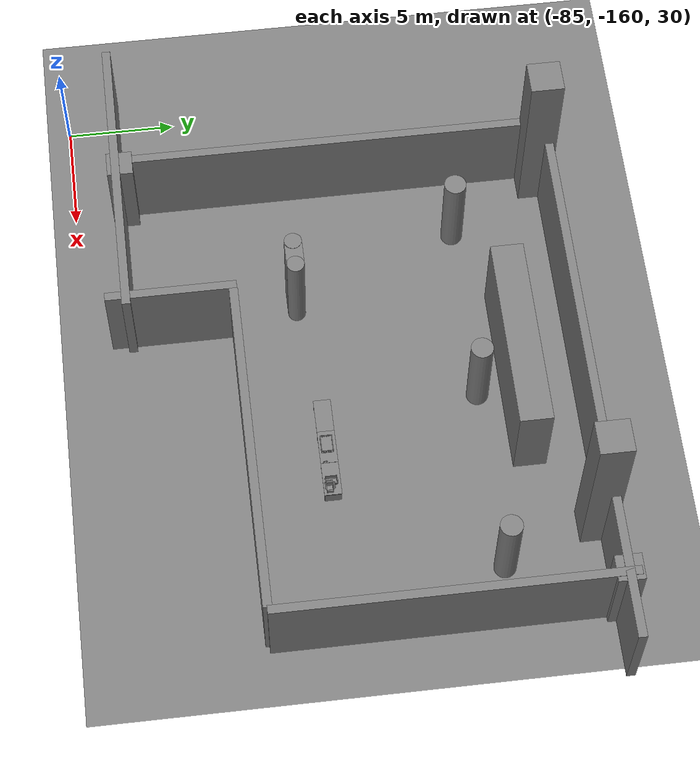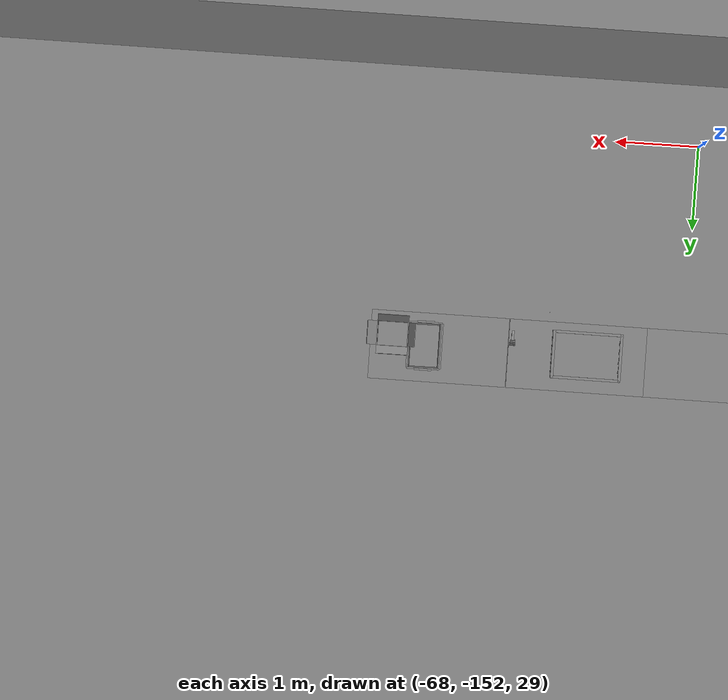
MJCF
<mujoco>
    <option gravity="0.000000000 0.000000000 -9.810000420" timestep="0.0049999999" integrator="implicitfast" density="1.225" viscosity="1.8000001e-05" noslip_iterations="10" iterations="100" sdf_iterations="50">
        <flag multiccd="disable"/>
    </option>
    <size memory="1000M"/>
    <compiler coordinate="local"/>
    <worldbody>
        <light cutoff="30" pos="0 1 1" dir="0 -1 -2"/>
        <light cutoff="30" pos="0 -1 1" dir="0 1 -2"/>
        <body pos="-64.866622925 -149.383972168 30.183746338" euler="89.999992371 89.999946594 0.000000000" name="openloong_gripper_2f85_fix_base_usda_bluebox_01">
            <geom contype="1" conaffinity="1" density="1000" type="box" material="" rgba="0.500000000 0.500000000 0.500000000 1.000000000" solimp="0.899999976 0.949999988 0.001000000" friction="1.000000000 0.005000000 0.000100000" solref="0.020000000 1.000000000" margin="0" condim="3" group="0" pos="0.276596069 0.187225342 0.000061035" quat="0.707107008 0.000077501 0.707106471 0.000077456" size="0.100000001 0.057999998 0.010000000" name="openloong_gripper_2f85_fix_base_usda_geom_B5A6C90F_A2A7_455E_9C18_9CCD1AA5C2E8"/>
            <geom contype="1" conaffinity="1" density="1000" type="box" material="" rgba="0.500000000 0.500000000 0.500000000 1.000000000" solimp="0.899999976 0.949999988 0.001000000" friction="1.000000000 0.005000000 0.000100000" solref="0.020000000 1.000000000" margin="0" condim="3" group="0" pos="0.000000000 0.002883911 0.000000000" quat="1.000000000 0.000000000 0.000000000 0.000000000" size="0.254000008 0.003000000 0.172000006" name="openloong_gripper_2f85_fix_base_usda_geom_3E6B3052_DE70_4038_9255_C73B10094C6F"/>
            <geom contype="1" conaffinity="1" density="1000" type="box" material="" rgba="0.500000000 0.500000000 0.500000000 1.000000000" solimp="0.899999976 0.949999988 0.001000000" friction="1.000000000 0.005000000 0.000100000" solref="0.020000000 1.000000000" margin="0" condim="3" group="0" pos="0.000015259 0.124874115 0.173477173" quat="0.999796450 0.020176515 -0.000000015 0.000000030" size="0.259999990 0.119999997 0.007000000" name="openloong_gripper_2f85_fix_base_usda_geom_67AC8460_C3E9_4D96_8EE7_A9C70884C272"/>
            <geom contype="1" conaffinity="1" density="1000" type="box" material="" rgba="0.500000000 0.500000000 0.500000000 1.000000000" solimp="0.899999976 0.949999988 0.001000000" friction="1.000000000 0.005000000 0.000100000" solref="0.020000000 1.000000000" margin="0" condim="3" group="0" pos="0.000015259 0.124874115 -0.173477173" quat="0.999796450 -0.020176545 -0.000000015 0.000000000" size="0.259999990 0.119999997 0.007000000" name="openloong_gripper_2f85_fix_base_usda_geom_AB01DD84_4AEA_49C2_AEE7_93CEED8724C6"/>
            <geom contype="1" conaffinity="1" density="1000" type="box" material="" rgba="0.500000000 0.500000000 0.500000000 1.000000000" solimp="0.899999976 0.949999988 0.001000000" friction="1.000000000 0.005000000 0.000100000" solref="0.020000000 1.000000000" margin="0" condim="3" group="0" pos="0.000015259 0.214012146 0.188980103" quat="0.999913096 0.013176724 0.000000015 0.000000000" size="0.259999990 0.029999999 0.012500000" name="openloong_gripper_2f85_fix_base_usda_geom_2893D9F0_CF2E_4F5F_89B0_38798B0CC22B"/>
            <geom contype="1" conaffinity="1" density="1000" type="box" material="" rgba="0.500000000 0.500000000 0.500000000 1.000000000" solimp="0.899999976 0.949999988 0.001000000" friction="1.000000000 0.005000000 0.000100000" solref="0.020000000 1.000000000" margin="0" condim="3" group="0" pos="-0.258346558 0.125289917 0.001876831" quat="0.702796996 -0.020792052 0.710783184 0.020769238" size="0.189999998 0.119999997 0.009000000" name="openloong_gripper_2f85_fix_base_usda_geom_E267EBD0_7C8A_47C5_814B_268B8245AC2A"/>
            <geom contype="1" conaffinity="1" density="1000" type="box" material="" rgba="0.500000000 0.500000000 0.500000000 1.000000000" solimp="0.899999976 0.949999988 0.001000000" friction="1.000000000 0.005000000 0.000100000" solref="0.020000000 1.000000000" margin="0" condim="3" group="0" pos="0.000015259 0.214012146 -0.188980103" quat="0.999913096 -0.013176769 0.000000030 0.000000015" size="0.259999990 0.029999999 0.012500000" name="openloong_gripper_2f85_fix_base_usda_geom_B5ED0D38_243F_4788_ACA0_561D594F92D7"/>
            <geom contype="1" conaffinity="1" density="1000" type="box" material="" rgba="0.500000000 0.500000000 0.500000000 1.000000000" solimp="0.899999976 0.949999988 0.001000000" friction="1.000000000 0.005000000 0.000100000" solref="0.020000000 1.000000000" margin="0" condim="3" group="0" pos="-0.276596069 0.187225342 0.000061035" quat="0.707106650 0.000077441 0.707106709 0.000077456" size="0.100000001 0.057999998 0.010000000" name="openloong_gripper_2f85_fix_base_usda_geom_2DA55E73_46E5_40FD_A5CB_7C22CFFE8965"/>
            <geom contype="1" conaffinity="1" density="1000" type="box" material="" rgba="0.500000000 0.500000000 0.500000000 1.000000000" solimp="0.899999976 0.949999988 0.001000000" friction="1.000000000 0.005000000 0.000100000" solref="0.020000000 1.000000000" margin="0" condim="3" group="0" pos="0.258346558 0.125289917 0.001876831" quat="0.702851534 0.018856451 0.710823834 -0.019329429" size="0.189999998 0.119999997 0.009000000" name="openloong_gripper_2f85_fix_base_usda_geom_6A9A5B69_26E6_4EDC_97E9_C78498BCA53F"/>
            <freejoint name="openloong_gripper_2f85_fix_base_usda_bluebox_01_joint"/>
            <site size="0.005000000 0.005000000 0.005000000" rgba="0.500000000 0.500000000 0.500000000 1.000000000" pos="0.000000000 0.000000000 0.000000000" quat="0.999961913 0.008726534 0.000000000 0.000000000" group="0" type="sphere" name="openloong_gripper_2f85_fix_base_usda_bluebox_01site"/>
        </body>
        <body pos="-64.496299744 -149.491867065 30.235729218" euler="0.000000000 0.000000000 89.999946594" name="openloong_gripper_2f85_fix_base_usda_cardboardbox_01">
            <geom contype="1" conaffinity="1" density="1000" type="box" material="" rgba="0.500000000 0.500000000 0.500000000 1.000000000" solimp="0.899999976 0.949999988 0.001000000" friction="1.000000000 0.005000000 0.000100000" solref="0.020000000 1.000000000" margin="0" condim="3" group="0" pos="-0.003166199 -0.004086494 0.005052090" quat="1.000000000 0.000000000 0.000000000 0.000000000" size="0.142499998 0.177500010 0.005000000" name="openloong_gripper_2f85_fix_base_usda_geom_2E8B0E84_9360_44F1_8620_1067C45F4C4B"/>
            <geom contype="1" conaffinity="1" density="1000" type="box" material="" rgba="0.500000000 0.500000000 0.500000000 1.000000000" solimp="0.899999976 0.949999988 0.001000000" friction="1.000000000 0.005000000 0.000100000" solref="0.020000000 1.000000000" margin="0" condim="3" group="0" pos="-0.003166199 0.170316696 0.150570869" quat="1.000000000 0.000000000 0.000000000 0.000000000" size="0.142499998 0.005000000 0.149999991" name="openloong_gripper_2f85_fix_base_usda_geom_6702C229_A151_4AB8_B9D9_46B7B0D10670"/>
            <geom contype="1" conaffinity="1" density="1000" type="box" material="" rgba="0.500000000 0.500000000 0.500000000 1.000000000" solimp="0.899999976 0.949999988 0.001000000" friction="1.000000000 0.005000000 0.000100000" solref="0.020000000 1.000000000" margin="0" condim="3" group="0" pos="-0.147399902 -0.005307198 0.150570869" quat="1.000000000 0.000000000 0.000000000 0.000000000" size="0.005000000 0.177500010 0.149999991" name="openloong_gripper_2f85_fix_base_usda_geom_3286E398_88FB_4E28_B81A_62C88DCE7B8B"/>
            <geom contype="1" conaffinity="1" density="1000" type="box" material="" rgba="0.500000000 0.500000000 0.500000000 1.000000000" solimp="0.899999976 0.949999988 0.001000000" friction="1.000000000 0.005000000 0.000100000" solref="0.020000000 1.000000000" margin="0" condim="3" group="0" pos="0.140275955 -0.005307198 0.150570869" quat="1.000000000 0.000000000 0.000000000 0.000000000" size="0.005000000 0.177500010 0.149999991" name="openloong_gripper_2f85_fix_base_usda_geom_957DA71A_E47C_4091_B253_826F9C59F50A"/>
            <geom contype="1" conaffinity="1" density="1000" type="box" material="" rgba="0.500000000 0.500000000 0.500000000 1.000000000" solimp="0.899999976 0.949999988 0.001000000" friction="1.000000000 0.005000000 0.000100000" solref="0.020000000 1.000000000" margin="0" condim="3" group="0" pos="-0.003166199 -0.181550980 0.150570869" quat="1.000000000 0.000000000 0.000000000 0.000000000" size="0.142499998 0.005000000 0.149999991" name="openloong_gripper_2f85_fix_base_usda_geom_1FA8FE1B_B38C_44F2_B005_773D2165EDC4"/>
            <freejoint name="openloong_gripper_2f85_fix_base_usda_cardboardbox_01_joint"/>
            <site size="0.005000000 0.005000000 0.005000000" rgba="0.500000000 0.500000000 0.500000000 1.000000000" pos="0.000000000 0.000000000 0.000000000" quat="0.999961913 0.008726535 0.000000000 0.000000000" group="0" type="sphere" name="openloong_gripper_2f85_fix_base_usda_site_6C18005E_4305_4C2C_868C_6535E27FBA9F"/>
            <body pos="0.139160156 -0.004048347 0.301930904" euler="-179.999954224 49.383502960 179.999954224" name="openloong_gripper_2f85_fix_base_usda_A1_006">
                <geom contype="1" conaffinity="1" density="1000" type="box" material="" rgba="0.500000000 0.500000000 0.500000000 1.000000000" solimp="0.899999976 0.949999988 0.001000000" friction="1.000000000 0.005000000 0.000100000" solref="0.020000000 1.000000000" margin="0" condim="3" group="0" pos="-0.071587563 0.000009537 0.001745224" quat="0.999999881 0.000000000 0.000000000 0.000000000" size="0.071249999 0.179999992 0.002500000" name="openloong_gripper_2f85_fix_base_usda_geom_B66F33B1_E363_47EC_ACC6_E5DD82687EF8"/>
                <joint armature="0" stiffness="0.07" damping="0.0099999998" axis="0.000000 1.000000 0.000000" type="hinge" name="openloong_gripper_2f85_fix_base_usda_A1_006"/>
            </body>
            <body pos="-0.145902634 -0.004086494 0.301938057" euler="-180.000000000 -60.000011444 -180.000000000" name="openloong_gripper_2f85_fix_base_usda_A2_006">
                <geom contype="1" conaffinity="1" density="1000" type="box" material="" rgba="0.500000000 0.500000000 0.500000000 1.000000000" solimp="0.899999976 0.949999988 0.001000000" friction="1.000000000 0.005000000 0.000100000" solref="0.020000000 1.000000000" margin="0" condim="3" group="0" pos="0.071268082 0.000009537 0.002717972" quat="0.000002921 0.000000000 -0.000000030 0.999999881" size="0.071249999 0.179999992 0.002500000" name="openloong_gripper_2f85_fix_base_usda_geom_2283A14D_0BA5_47B7_A90C_56A9B5D602ED"/>
                <joint armature="0" stiffness="0.07" damping="0.0099999998" axis="0.000000 1.000000 0.000000" type="hinge" name="openloong_gripper_2f85_fix_base_usda_A2_006"/>
            </body>
            <body pos="-0.003385544 0.175991058 0.301930904" euler="-125.858116150 -0.000004561 0.000002331" name="openloong_gripper_2f85_fix_base_usda_B2_006">
                <geom contype="1" conaffinity="1" density="1000" type="box" material="" rgba="0.500000000 0.500000000 0.500000000 1.000000000" solimp="0.899999976 0.949999988 0.001000000" friction="1.000000000 0.005000000 0.000100000" solref="0.020000000 1.000000000" margin="0" condim="3" group="0" pos="0.000009537 -0.070939064 -0.002470016" quat="0.999614120 0.027776197 -0.000000015 0.000000030" size="0.137500003 0.064999998 0.005000000" name="openloong_gripper_2f85_fix_base_usda_geom_BB9EE97C_F3F2_4B58_8AC2_A8EA0C61FCDF"/>
                <joint armature="0" stiffness="0.07" damping="0.0099999998" axis="1.000000 0.000000 0.000000" type="hinge" name="openloong_gripper_2f85_fix_base_usda_B2_006"/>
            </body>
            <body pos="-0.003385544 -0.184140205 0.301938057" euler="147.805557251 0.000000000 0.000000000" name="openloong_gripper_2f85_fix_base_usda_B1_006">
                <geom contype="1" conaffinity="1" density="1000" type="box" material="" rgba="0.500000000 0.500000000 0.500000000 1.000000000" solimp="0.899999976 0.949999988 0.001000000" friction="1.000000000 0.005000000 0.000100000" solref="0.020000000 1.000000000" margin="0" condim="3" group="0" pos="-0.000028610 0.070202351 -0.002703667" quat="0.999614179 -0.027776167 0.000000000 0.000000000" size="0.137500003 0.064999998 0.005000000" name="openloong_gripper_2f85_fix_base_usda_geom_34C773CF_C03F_4AB8_BEA8_D22569137745"/>
                <joint armature="0" stiffness="0.07" damping="0.0099999998" axis="1.000000 0.000000 0.000000" type="hinge" name="openloong_gripper_2f85_fix_base_usda_B1_006"/>
            </body>
        </body>
        <body pos="-65.882858276 -149.481979370 30.229999542" euler="-64.487716675 0.000000000 0.000000000" name="openloong_gripper_2f85_fix_base_usda_Barcode">
            <geom contype="1" conaffinity="1" density="1000" type="box" material="" rgba="0.500000000 0.500000000 0.500000000 1.000000000" solimp="0.899999976 0.949999988 0.001000000" friction="1.000000000 0.005000000 0.000100000" solref="0.020000000 1.000000000" margin="0" condim="3" group="0" pos="0.000000000 0.013038635 0.001419067" quat="0.000000000 0.000000000 0.000000000 1.000000119" size="0.034000002 0.010000000 0.017999999" name="openloong_gripper_2f85_fix_base_usda_geom_AC47BB93_CED4_4874_A93B_41A8B1BC0676"/>
            <geom contype="1" conaffinity="1" density="1000" type="box" material="" rgba="0.500000000 0.500000000 0.500000000 1.000000000" solimp="0.899999976 0.949999988 0.001000000" friction="1.000000000 0.005000000 0.000100000" solref="0.020000000 1.000000000" margin="0" condim="3" group="0" pos="0.000000000 -0.035301208 -0.007095337" quat="0.000000000 0.000000000 -0.043619365 0.999048233" size="0.028999999 0.010000000 0.020000000" name="openloong_gripper_2f85_fix_base_usda_geom_29B5455E_8171_4FB3_BE48_D0230AA8596A"/>
            <geom contype="1" conaffinity="1" density="1000" type="box" material="" rgba="0.500000000 0.500000000 0.500000000 1.000000000" solimp="0.899999976 0.949999988 0.001000000" friction="1.000000000 0.005000000 0.000100000" solref="0.020000000 1.000000000" margin="0" condim="3" group="0" pos="0.000000000 -0.043411255 -0.011749268" quat="0.922262907 0.386563420 0.000000000 0.000000000" size="0.026000001 0.010000000 0.020000000" name="openloong_gripper_2f85_fix_base_usda_geom_87D8B996_A568_4505_BCB2_0FFDF19A271A"/>
            <geom contype="1" conaffinity="1" density="1000" type="box" material="" rgba="0.500000000 0.500000000 0.500000000 1.000000000" solimp="0.899999976 0.949999988 0.001000000" friction="1.000000000 0.005000000 0.000100000" solref="0.020000000 1.000000000" margin="0" condim="3" group="0" pos="0.000000000 -0.016967773 -0.031860352" quat="0.000000000 0.000000000 0.000000000 1.000000119" size="0.008000000 0.010000000 0.013000000" name="openloong_gripper_2f85_fix_base_usda_geom_20AE5C99_1D21_4B45_8CDA_F3623D99298A"/>
            <geom contype="1" conaffinity="1" density="1000" type="box" material="" rgba="0.500000000 0.500000000 0.500000000 1.000000000" solimp="0.899999976 0.949999988 0.001000000" friction="1.000000000 0.005000000 0.000100000" solref="0.020000000 1.000000000" margin="0" condim="3" group="0" pos="0.000000000 -0.001869202 0.000312805" quat="0.953716993 0.300705761 0.000000000 0.000000000" size="0.032000002 0.010000000 0.018999999" name="openloong_gripper_2f85_fix_base_usda_geom_A87D80AC_69B4_45EB_BF05_DA122214C0B2"/>
            <geom contype="1" conaffinity="1" density="1000" type="box" material="" rgba="0.500000000 0.500000000 0.500000000 1.000000000" solimp="0.899999976 0.949999988 0.001000000" friction="1.000000000 0.005000000 0.000100000" solref="0.020000000 1.000000000" margin="0" condim="3" group="0" pos="0.000000000 -0.019531250 -0.003173828" quat="0.953716993 0.300705761 0.000000000 0.000000000" size="0.030999999 0.010000000 0.020000000" name="openloong_gripper_2f85_fix_base_usda_geom_DB2052E0_5060_49DB_A041_E72C123F7CC8"/>
            <geom contype="1" conaffinity="1" density="1000" type="box" material="" rgba="0.500000000 0.500000000 0.500000000 1.000000000" solimp="0.899999976 0.949999988 0.001000000" friction="1.000000000 0.005000000 0.000100000" solref="0.020000000 1.000000000" margin="0" condim="3" group="0" pos="0.000000000 -0.035301208 -0.007095337" quat="0.953716993 0.300705761 0.000000000 0.000000000" size="0.028999999 0.010000000 0.020000000" name="openloong_gripper_2f85_fix_base_usda_geom_786A0B56_F71C_403E_B7EC_34BCFC3F14E0"/>
            <geom contype="1" conaffinity="1" density="1000" type="box" material="" rgba="0.500000000 0.500000000 0.500000000 1.000000000" solimp="0.899999976 0.949999988 0.001000000" friction="1.000000000 0.005000000 0.000100000" solref="0.020000000 1.000000000" margin="0" condim="3" group="0" pos="0.000000000 -0.042617798 -0.071121216" quat="0.000000000 0.000000000 0.000000000 1.000000119" size="0.013000000 0.021000000 0.059999999" name="openloong_gripper_2f85_fix_base_usda_geom_099F9FFC_3EFE_4D09_BD41_0CB20A7A1A52"/>
            <freejoint name="openloong_gripper_2f85_fix_base_usda_Barcode_joint"/>
            <site size="0.005000000 0.005000000 0.005000000" rgba="0.500000000 0.500000000 0.500000000 1.000000000" pos="0.000000000 0.000000000 0.000000000" quat="1.000000000 0.000000000 0.000000000 0.000000000" group="0" type="sphere" name="openloong_gripper_2f85_fix_base_usda_Barcode_site"/>
        </body>
        <body pos="-66.745018005 -149.392349243 30.184000015" euler="0.000000000 0.000000000 89.999946594" name="[22331878433243]_Basket_01">
            <geom contype="1" conaffinity="1" density="1000" type="box" material="" rgba="0.500000000 0.500000000 0.500000000 1.000000000" solimp="0.899999976 0.949999988 0.001000000" friction="1.000000000 0.005000000 0.000100000" solref="0.020000000 1.000000000" margin="0" condim="3" group="0" pos="-0.052425385 0.389207840 0.089787483" quat="0.707107008 0.000000000 0.000000000 0.707106411" size="0.014249999 0.014249999 0.059999999" name="[22331878433243]_geom_2933FD9E_6644_4891_9381_BAA207F2BF3B"/>
            <geom contype="1" conaffinity="1" density="1000" type="box" material="" rgba="0.500000000 0.500000000 0.500000000 1.000000000" solimp="0.899999976 0.949999988 0.001000000" friction="1.000000000 0.005000000 0.000100000" solref="0.020000000 1.000000000" margin="0" condim="3" group="0" pos="0.264015198 -0.133043289 0.089787483" quat="0.707107008 0.000000000 0.000000000 0.707106411" size="0.014249999 0.014249999 0.059999999" name="[22331878433243]_geom_54253B66_300A_4D3D_85C7_5F246023D04E"/>
            <geom contype="1" conaffinity="1" density="1000" type="box" material="" rgba="0.500000000 0.500000000 0.500000000 1.000000000" solimp="0.899999976 0.949999988 0.001000000" friction="1.000000000 0.005000000 0.000100000" solref="0.020000000 1.000000000" margin="0" condim="3" group="0" pos="-0.264015198 -0.265548706 0.089793205" quat="0.707107008 0.000000000 0.000000000 0.707106411" size="0.014249999 0.014249999 0.059999999" name="[22331878433243]_geom_860CCCE6_0769_43ED_93B8_6695D53E1E8C"/>
            <geom contype="1" conaffinity="1" density="1000" type="box" material="" rgba="0.500000000 0.500000000 0.500000000 1.000000000" solimp="0.899999976 0.949999988 0.001000000" friction="1.000000000 0.005000000 0.000100000" solref="0.020000000 1.000000000" margin="0" condim="3" group="0" pos="-0.160263062 -0.389322281 0.089793205" quat="0.707107008 0.000000000 0.000000000 0.707106411" size="0.014249999 0.014249999 0.059999999" name="[22331878433243]_geom_3D150A04_0631_4454_9ADD_9F507E5E5B7C"/>
            <geom contype="1" conaffinity="1" density="1000" type="box" material="" rgba="0.500000000 0.500000000 0.500000000 1.000000000" solimp="0.899999976 0.949999988 0.001000000" friction="1.000000000 0.005000000 0.000100000" solref="0.020000000 1.000000000" margin="0" condim="3" group="0" pos="0.162265778 -0.389322281 0.089787483" quat="0.707107008 0.000000000 0.000000000 0.707106411" size="0.014249999 0.014249999 0.059999999" name="[22331878433243]_geom_EC4622AB_86BC_471D_9710_154D88DFE08E"/>
            <geom contype="1" conaffinity="1" density="1000" type="box" material="" rgba="0.500000000 0.500000000 0.500000000 1.000000000" solimp="0.899999976 0.949999988 0.001000000" friction="1.000000000 0.005000000 0.000100000" solref="0.020000000 1.000000000" margin="0" condim="3" group="0" pos="0.264015198 0.389207840 0.089787483" quat="0.707107008 0.000000000 0.000000000 0.707106411" size="0.014249999 0.014249999 0.059999999" name="[22331878433243]_geom_CA393FB3_19D2_4210_B023_30501B9FAE42"/>
            <geom contype="1" conaffinity="1" density="1000" type="box" material="" rgba="0.500000000 0.500000000 0.500000000 1.000000000" solimp="0.899999976 0.949999988 0.001000000" friction="1.000000000 0.005000000 0.000100000" solref="0.020000000 1.000000000" margin="0" condim="3" group="0" pos="-0.264015198 -0.133043289 0.089793205" quat="0.707107008 0.000000000 0.000000000 0.707106411" size="0.014249999 0.014249999 0.059999999" name="[22331878433243]_geom_93CCDCC0_9820_44E6_BB31_3218FB16AA47"/>
            <geom contype="1" conaffinity="1" density="1000" type="box" material="" rgba="0.500000000 0.500000000 0.500000000 1.000000000" solimp="0.899999976 0.949999988 0.001000000" friction="1.000000000 0.005000000 0.000100000" solref="0.020000000 1.000000000" margin="0" condim="3" group="0" pos="-0.264026642 0.269256592 0.089793205" quat="0.707107008 0.000000000 0.000000000 0.707106411" size="0.014249999 0.014249999 0.059999999" name="[22331878433243]_geom_B5571A87_00A8_41B6_8032_8BDFA21174F8"/>
            <geom contype="1" conaffinity="1" density="1000" type="box" material="" rgba="0.500000000 0.500000000 0.500000000 1.000000000" solimp="0.899999976 0.949999988 0.001000000" friction="1.000000000 0.005000000 0.000100000" solref="0.020000000 1.000000000" margin="0" condim="3" group="0" pos="0.054462433 0.389207840 0.089787483" quat="0.707107008 0.000000000 0.000000000 0.707106411" size="0.014249999 0.014249999 0.059999999" name="[22331878433243]_geom_3AB7E0E6_DE89_4246_B94F_8E1C83FBB076"/>
            <geom contype="1" conaffinity="1" density="1000" type="box" material="" rgba="0.500000000 0.500000000 0.500000000 1.000000000" solimp="0.899999976 0.949999988 0.001000000" friction="1.000000000 0.005000000 0.000100000" solref="0.020000000 1.000000000" margin="0" condim="3" group="0" pos="0.054462433 -0.389322281 0.089787483" quat="0.707107008 0.000000000 0.000000000 0.707106411" size="0.014249999 0.014249999 0.059999999" name="[22331878433243]_geom_A85535DC_7DBF_4188_AE17_231BE7D1C004"/>
            <geom contype="1" conaffinity="1" density="1000" type="box" material="" rgba="0.500000000 0.500000000 0.500000000 1.000000000" solimp="0.899999976 0.949999988 0.001000000" friction="1.000000000 0.005000000 0.000100000" solref="0.020000000 1.000000000" margin="0" condim="3" group="0" pos="0.264015198 0.269256592 0.089793205" quat="0.707107008 0.000000000 0.000000000 0.707106411" size="0.014249999 0.014249999 0.059999999" name="[22331878433243]_geom_A491C9FB_A8B1_4DDE_9903_38CA4F7F1195"/>
            <geom contype="1" conaffinity="1" density="1000" type="box" material="" rgba="0.500000000 0.500000000 0.500000000 1.000000000" solimp="0.899999976 0.949999988 0.001000000" friction="1.000000000 0.005000000 0.000100000" solref="0.020000000 1.000000000" margin="0" condim="3" group="0" pos="0.264015198 -0.389322281 0.089787483" quat="0.707107008 0.000000000 0.000000000 0.707106411" size="0.014249999 0.014249999 0.059999999" name="[22331878433243]_geom_9FE43D3C_22FB_49A9_AF7F_2F6F2D112BEC"/>
            <geom contype="1" conaffinity="1" density="1000" type="box" material="" rgba="0.500000000 0.500000000 0.500000000 1.000000000" solimp="0.899999976 0.949999988 0.001000000" friction="1.000000000 0.005000000 0.000100000" solref="0.020000000 1.000000000" margin="0" condim="3" group="0" pos="0.000000000 0.000000000 0.015998840" quat="0.707107008 0.000000000 0.000000000 0.707106411" size="0.403499991 0.279000014 0.015750000" name="[22331878433243]_geom_6B730F86_3BFB_4E89_920F_0FAFE4EE3581"/>
            <geom contype="1" conaffinity="1" density="1000" type="box" material="" rgba="0.500000000 0.500000000 0.500000000 1.000000000" solimp="0.899999976 0.949999988 0.001000000" friction="1.000000000 0.005000000 0.000100000" solref="0.020000000 1.000000000" margin="0" condim="3" group="0" pos="0.000000000 -0.389476776 0.163619041" quat="0.707107008 0.000000000 0.000000000 0.707106411" size="0.015000000 0.277500004 0.015750000" name="[22331878433243]_geom_0C97AEA4_8949_4957_950B_A8AEFA100E04"/>
            <geom contype="1" conaffinity="1" density="1000" type="box" material="" rgba="0.500000000 0.500000000 0.500000000 1.000000000" solimp="0.899999976 0.949999988 0.001000000" friction="1.000000000 0.005000000 0.000100000" solref="0.020000000 1.000000000" margin="0" condim="3" group="0" pos="0.162265778 0.389207840 0.089787483" quat="0.707107008 0.000000000 0.000000000 0.707106411" size="0.014249999 0.014249999 0.059999999" name="[22331878433243]_geom_4D6187EA_C153_4D7F_AE2D_DBD32A29C1A9"/>
            <geom contype="1" conaffinity="1" density="1000" type="box" material="" rgba="0.500000000 0.500000000 0.500000000 1.000000000" solimp="0.899999976 0.949999988 0.001000000" friction="1.000000000 0.005000000 0.000100000" solref="0.020000000 1.000000000" margin="0" condim="3" group="0" pos="0.000000000 0.389471054 0.163619041" quat="0.707107008 0.000000000 0.000000000 0.707106411" size="0.015000000 0.277500004 0.015750000" name="[22331878433243]_geom_F78BEC76_900D_4C42_8C43_9441E558D430"/>
            <geom contype="1" conaffinity="1" density="1000" type="box" material="" rgba="0.500000000 0.500000000 0.500000000 1.000000000" solimp="0.899999976 0.949999988 0.001000000" friction="1.000000000 0.005000000 0.000100000" solref="0.020000000 1.000000000" margin="0" condim="3" group="0" pos="-0.263511658 0.000000000 0.163619041" quat="0.707107008 0.000000000 0.000000000 0.707106411" size="0.403499991 0.015000000 0.015750000" name="[22331878433243]_geom_F09761E7_6834_45FB_BFC5_EA0D9227F7B6"/>
            <geom contype="1" conaffinity="1" density="1000" type="box" material="" rgba="0.500000000 0.500000000 0.500000000 1.000000000" solimp="0.899999976 0.949999988 0.001000000" friction="1.000000000 0.005000000 0.000100000" solref="0.020000000 1.000000000" margin="0" condim="3" group="0" pos="-0.264015198 0.141334534 0.089793205" quat="0.707107008 0.000000000 0.000000000 0.707106411" size="0.014249999 0.014249999 0.059999999" name="[22331878433243]_geom_5DC3327B_EDEE_4070_B77E_9C1139C9C26B"/>
            <geom contype="1" conaffinity="1" density="1000" type="box" material="" rgba="0.500000000 0.500000000 0.500000000 1.000000000" solimp="0.899999976 0.949999988 0.001000000" friction="1.000000000 0.005000000 0.000100000" solref="0.020000000 1.000000000" margin="0" condim="3" group="0" pos="0.264015198 -0.265548706 0.089787483" quat="0.707107008 0.000000000 0.000000000 0.707106411" size="0.014249999 0.014249999 0.059999999" name="[22331878433243]_geom_6E4E5485_FFD1_4C8F_A8B9_29CCE4C97514"/>
            <geom contype="1" conaffinity="1" density="1000" type="box" material="" rgba="0.500000000 0.500000000 0.500000000 1.000000000" solimp="0.899999976 0.949999988 0.001000000" friction="1.000000000 0.005000000 0.000100000" solref="0.020000000 1.000000000" margin="0" condim="3" group="0" pos="-0.160263062 0.389207840 0.089787483" quat="0.707107008 0.000000000 0.000000000 0.707106411" size="0.014249999 0.014249999 0.059999999" name="[22331878433243]_geom_2D13EEE4_E44D_416F_A49A_123A59330A29"/>
            <geom contype="1" conaffinity="1" density="1000" type="box" material="" rgba="0.500000000 0.500000000 0.500000000 1.000000000" solimp="0.899999976 0.949999988 0.001000000" friction="1.000000000 0.005000000 0.000100000" solref="0.020000000 1.000000000" margin="0" condim="3" group="0" pos="-0.052425385 -0.389322281 0.089787483" quat="0.707107008 0.000000000 0.000000000 0.707106411" size="0.014249999 0.014249999 0.059999999" name="[22331878433243]_geom_819A7CD8_57E2_45F4_9C66_004CBDDB128F"/>
            <geom contype="1" conaffinity="1" density="1000" type="box" material="" rgba="0.500000000 0.500000000 0.500000000 1.000000000" solimp="0.899999976 0.949999988 0.001000000" friction="1.000000000 0.005000000 0.000100000" solref="0.020000000 1.000000000" margin="0" condim="3" group="0" pos="-0.264026642 -0.389322281 0.089793205" quat="0.707107008 0.000000000 0.000000000 0.707106411" size="0.014249999 0.014249999 0.059999999" name="[22331878433243]_geom_79B00F09_F285_412B_97CD_5F75E152AC17"/>
            <geom contype="1" conaffinity="1" density="1000" type="box" material="" rgba="0.500000000 0.500000000 0.500000000 1.000000000" solimp="0.899999976 0.949999988 0.001000000" friction="1.000000000 0.005000000 0.000100000" solref="0.020000000 1.000000000" margin="0" condim="3" group="0" pos="0.264015198 0.141334534 0.089787483" quat="0.707107008 0.000000000 0.000000000 0.707106411" size="0.014249999 0.014249999 0.059999999" name="[22331878433243]_geom_F929F1DF_EF73_4388_ADE4_0B3AA0F25D31"/>
            <geom contype="1" conaffinity="1" density="1000" type="box" material="" rgba="0.500000000 0.500000000 0.500000000 1.000000000" solimp="0.899999976 0.949999988 0.001000000" friction="1.000000000 0.005000000 0.000100000" solref="0.020000000 1.000000000" margin="0" condim="3" group="0" pos="-0.264015198 0.389207840 0.089793205" quat="0.707107008 0.000000000 0.000000000 0.707106411" size="0.014249999 0.014249999 0.059999999" name="[22331878433243]_geom_472651E9_B2A9_4FF1_872F_EC367303AC7B"/>
            <geom contype="1" conaffinity="1" density="1000" type="box" material="" rgba="0.500000000 0.500000000 0.500000000 1.000000000" solimp="0.899999976 0.949999988 0.001000000" friction="1.000000000 0.005000000 0.000100000" solref="0.020000000 1.000000000" margin="0" condim="3" group="0" pos="0.264015198 0.004480362 0.089787483" quat="0.707107008 0.000000000 0.000000000 0.707106411" size="0.014249999 0.014249999 0.059999999" name="[22331878433243]_geom_F84F2AF8_9033_42CC_BE79_57D17960CBF9"/>
            <geom contype="1" conaffinity="1" density="1000" type="box" material="" rgba="0.500000000 0.500000000 0.500000000 1.000000000" solimp="0.899999976 0.949999988 0.001000000" friction="1.000000000 0.005000000 0.000100000" solref="0.020000000 1.000000000" margin="0" condim="3" group="0" pos="0.263694763 -0.000011444 0.163619041" quat="0.707107008 0.000000000 0.000000000 0.707106411" size="0.403499991 0.015000000 0.015750000" name="[22331878433243]_geom_6F37FFFD_2180_4225_A1F7_E878236E5337"/>
            <geom contype="1" conaffinity="1" density="1000" type="box" material="" rgba="0.500000000 0.500000000 0.500000000 1.000000000" solimp="0.899999976 0.949999988 0.001000000" friction="1.000000000 0.005000000 0.000100000" solref="0.020000000 1.000000000" margin="0" condim="3" group="0" pos="-0.264015198 0.004480362 0.089793205" quat="0.707107008 0.000000000 0.000000000 0.707106411" size="0.014249999 0.014249999 0.059999999" name="[22331878433243]_geom_180C58A0_4D9B_4587_A9F8_701E4134E68C"/>
            <freejoint name="[22331878433243]_joint_FB57D496_9D8C_488B_AC3A_7D5D658973E1"/>
        </body>
        <body pos="0.000000000 0.000000000 0.000000000" euler="0.000000000 0.000000000 0.000000000" name="Static Objects_Static Objects">
            <geom contype="1" conaffinity="1" density="1000" type="box" material="" rgba="0.500000000 0.500000000 0.500000000 1.000000000" solimp="0.899999976 0.949999988 0.001000000" friction="1.000000000 0.005000000 0.000100000" solref="0.020000000 1.000000000" margin="0" condim="3" group="0" pos="-67.544113159 -149.365814209 29.727830887" quat="0.500000417 0.499999970 0.499999553 0.499999970" size="0.381000012 0.319999993 0.041000001" name="Static Objects_geom_FBE72ECE_B190_4B56_B9C9_432382562741"/>
            <geom contype="1" conaffinity="1" density="1000" type="box" material="" rgba="0.500000000 0.500000000 0.500000000 1.000000000" solimp="0.899999976 0.949999988 0.001000000" friction="1.000000000 0.005000000 0.000100000" solref="0.020000000 1.000000000" margin="0" condim="3" group="0" pos="-68.239501953 -149.365814209 30.086868286" quat="0.500000417 0.499999970 0.499999553 0.499999970" size="0.370999992 0.039500002 0.745000005" name="Static Objects_geom_3B0D19F8_F581_4EA2_8258_293B5ECE9500"/>
            <geom contype="1" conaffinity="1" density="1000" type="box" material="" rgba="0.500000000 0.500000000 0.500000000 1.000000000" solimp="0.899999976 0.949999988 0.001000000" friction="1.000000000 0.005000000 0.000100000" solref="0.020000000 1.000000000" margin="0" condim="3" group="0" pos="-68.239501953 -149.365814209 30.147235870" quat="0.500000417 0.499999970 0.499999553 0.499999970" size="0.400000006 0.022000000 0.800000012" name="Static Objects_geom_689945C9_28E0_49AE_A397_565861579F92"/>
            <geom contype="1" conaffinity="1" density="1000" type="box" material="" rgba="0.500000000 0.500000000 0.500000000 1.000000000" solimp="0.899999976 0.949999988 0.001000000" friction="1.000000000 0.005000000 0.000100000" solref="0.020000000 1.000000000" margin="0" condim="3" group="0" pos="-68.934890747 -149.365814209 29.727830887" quat="0.500000417 0.499999970 0.499999553 0.499999970" size="0.381000012 0.319999993 0.041000001" name="Static Objects_geom_BBCD7663_3027_49D9_B1B1_3F12FFD34F80"/>
            <geom contype="1" conaffinity="1" density="1000" type="box" material="" rgba="0.500000000 0.500000000 0.500000000 1.000000000" solimp="0.899999976 0.949999988 0.001000000" friction="1.000000000 0.005000000 0.000100000" solref="0.020000000 1.000000000" margin="0" condim="3" group="0" pos="-68.239501953 -149.365814209 29.561563492" quat="0.500000417 0.499999970 0.499999553 0.499999970" size="0.020000000 0.022000000 0.660000026" name="Static Objects_geom_70EBAB1C_A789_4A75_8FFE_2BB5C9B1E06C"/>
            <geom contype="1" conaffinity="1" density="1000" type="box" material="" rgba="0.500000000 0.500000000 0.500000000 1.000000000" solimp="0.899999976 0.949999988 0.001000000" friction="1.000000000 0.005000000 0.000100000" solref="0.020000000 1.000000000" margin="0" condim="3" group="0" pos="-65.945671082 -149.365814209 29.727830887" quat="0.500000417 0.499999970 0.499999553 0.499999970" size="0.381000012 0.319999993 0.041000001" name="Static Objects_geom_E8223037_C029_4E07_970D_A1EA13805D87"/>
            <geom contype="1" conaffinity="1" density="1000" type="box" material="" rgba="0.500000000 0.500000000 0.500000000 1.000000000" solimp="0.899999976 0.949999988 0.001000000" friction="1.000000000 0.005000000 0.000100000" solref="0.020000000 1.000000000" margin="0" condim="3" group="0" pos="-66.641059875 -149.365814209 30.086868286" quat="0.500000417 0.499999970 0.499999553 0.499999970" size="0.370999992 0.039500002 0.745000005" name="Static Objects_geom_403584CB_D166_4B00_B390_3CB36CEA08B6"/>
            <geom contype="1" conaffinity="1" density="1000" type="box" material="" rgba="0.500000000 0.500000000 0.500000000 1.000000000" solimp="0.899999976 0.949999988 0.001000000" friction="1.000000000 0.005000000 0.000100000" solref="0.020000000 1.000000000" margin="0" condim="3" group="0" pos="-66.641059875 -149.365814209 30.147235870" quat="0.500000417 0.499999970 0.499999553 0.499999970" size="0.400000006 0.022000000 0.800000012" name="Static Objects_geom_BA9D9392_1274_4F2E_ABA4_2A99D45C0812"/>
            <geom contype="1" conaffinity="1" density="1000" type="box" material="" rgba="0.500000000 0.500000000 0.500000000 1.000000000" solimp="0.899999976 0.949999988 0.001000000" friction="1.000000000 0.005000000 0.000100000" solref="0.020000000 1.000000000" margin="0" condim="3" group="0" pos="-67.336448669 -149.365814209 29.727830887" quat="0.500000417 0.499999970 0.499999553 0.499999970" size="0.381000012 0.319999993 0.041000001" name="Static Objects_geom_F73AEE30_2C2D_4F10_B1DA_CD5EC1E600FE"/>
            <geom contype="1" conaffinity="1" density="1000" type="box" material="" rgba="0.500000000 0.500000000 0.500000000 1.000000000" solimp="0.899999976 0.949999988 0.001000000" friction="1.000000000 0.005000000 0.000100000" solref="0.020000000 1.000000000" margin="0" condim="3" group="0" pos="-66.641059875 -149.365814209 29.561563492" quat="0.500000417 0.499999970 0.499999553 0.499999970" size="0.020000000 0.022000000 0.660000026" name="Static Objects_geom_ECAF9027_5561_4D9F_AD73_DB98C53E31C1"/>
            <geom contype="1" conaffinity="1" density="1000" type="box" material="" rgba="0.500000000 0.500000000 0.500000000 1.000000000" solimp="0.899999976 0.949999988 0.001000000" friction="1.000000000 0.005000000 0.000100000" solref="0.020000000 1.000000000" margin="0" condim="3" group="0" pos="-64.338577271 -149.365814209 29.727830887" quat="0.500000417 0.499999970 0.499999553 0.499999970" size="0.381000012 0.319999993 0.041000001" name="Static Objects_geom_6F25E6AD_84DF_4519_8F95_53365A1FF7AD"/>
            <geom contype="1" conaffinity="1" density="1000" type="box" material="" rgba="0.500000000 0.500000000 0.500000000 1.000000000" solimp="0.899999976 0.949999988 0.001000000" friction="1.000000000 0.005000000 0.000100000" solref="0.020000000 1.000000000" margin="0" condim="3" group="0" pos="-65.033966064 -149.365814209 30.086868286" quat="0.500000417 0.499999970 0.499999553 0.499999970" size="0.370999992 0.039500002 0.745000005" name="Static Objects_geom_BA2F9063_4C0D_4C79_882D_8657D42DE509"/>
            <geom contype="1" conaffinity="1" density="1000" type="box" material="" rgba="0.500000000 0.500000000 0.500000000 1.000000000" solimp="0.899999976 0.949999988 0.001000000" friction="1.000000000 0.005000000 0.000100000" solref="0.020000000 1.000000000" margin="0" condim="3" group="0" pos="-65.033966064 -149.365814209 30.147235870" quat="0.500000417 0.499999970 0.499999553 0.499999970" size="0.400000006 0.022000000 0.800000012" name="Static Objects_geom_4CE820BA_E8F4_458C_8FC1_3217645D2187"/>
            <geom contype="1" conaffinity="1" density="1000" type="box" material="" rgba="0.500000000 0.500000000 0.500000000 1.000000000" solimp="0.899999976 0.949999988 0.001000000" friction="1.000000000 0.005000000 0.000100000" solref="0.020000000 1.000000000" margin="0" condim="3" group="0" pos="-65.729354858 -149.365814209 29.727830887" quat="0.500000417 0.499999970 0.499999553 0.499999970" size="0.381000012 0.319999993 0.041000001" name="Static Objects_geom_434CC557_34F2_4F16_A0C3_0118A167C2B0"/>
            <geom contype="1" conaffinity="1" density="1000" type="box" material="" rgba="0.500000000 0.500000000 0.500000000 1.000000000" solimp="0.899999976 0.949999988 0.001000000" friction="1.000000000 0.005000000 0.000100000" solref="0.020000000 1.000000000" margin="0" condim="3" group="0" pos="-65.033966064 -149.365814209 29.561563492" quat="0.500000417 0.499999970 0.499999553 0.499999970" size="0.020000000 0.022000000 0.660000026" name="Static Objects_geom_014C28A3_8DD5_497E_BF55_01E2407A2E9E"/>
            <geom contype="1" conaffinity="1" density="1000" type="box" material="" rgba="0.500000000 0.500000000 0.500000000 1.000000000" solimp="0.899999976 0.949999988 0.001000000" friction="1.000000000 0.005000000 0.000100000" solref="0.020000000 1.000000000" margin="0" condim="3" group="0" pos="-61.754566193 -137.853729248 33.906845093" quat="0.707107067 0.000000000 0.000000000 0.707106471" size="0.759999990 0.759999990 4.500000000" name="Static Objects_geom_6A785B2A_2E01_41C0_8614_5DD10B8545BC"/>
            <geom contype="1" conaffinity="1" density="1000" type="box" material="" rgba="0.500000000 0.500000000 0.500000000 1.000000000" solimp="0.899999976 0.949999988 0.001000000" friction="1.000000000 0.005000000 0.000100000" solref="0.020000000 1.000000000" margin="0" condim="3" group="0" pos="-57.511135101 -144.927108765 31.707921982" quat="1.000000000 0.000000000 0.000000000 0.000000000" size="0.200000003 8.000000000 2.299999952" name="Static Objects_geom_82760961_C87F_47FF_AFFA_1F933EE8370C"/>
            <geom contype="1" conaffinity="1" density="1000" type="box" material="" rgba="0.500000000 0.500000000 0.500000000 1.000000000" solimp="0.899999976 0.949999988 0.001000000" friction="1.000000000 0.005000000 0.000100000" solref="0.020000000 1.000000000" margin="0" condim="3" group="0" pos="-80.517646790 -157.574050903 31.688196182" quat="0.707107067 0.000000000 0.000000000 0.707106471" size="0.600000024 0.600000024 2.299999952" name="Static Objects_geom_DC12A655_D169_4571_BCA8_205798C6253C"/>
            <geom contype="1" conaffinity="1" density="1000" type="box" material="" rgba="0.500000000 0.500000000 0.500000000 1.000000000" solimp="0.899999976 0.949999988 0.001000000" friction="1.000000000 0.005000000 0.000100000" solref="0.020000000 1.000000000" margin="0" condim="3" group="0" pos="-80.711044312 -147.414932251 31.666158676" quat="1.000000000 0.000000000 0.000000000 0.000000000" size="0.200000003 10.000000000 2.299999952" name="Static Objects_geom_673F39F9_1952_4C66_B6C0_84CF739CC832"/>
            <geom contype="1" conaffinity="1" density="1000" type="box" material="" rgba="0.500000000 0.500000000 0.500000000 1.000000000" solimp="0.899999976 0.949999988 0.001000000" friction="1.000000000 0.005000000 0.000100000" solref="0.020000000 1.000000000" margin="0" condim="3" group="0" pos="-57.687217712 -137.434692383 31.688196182" quat="0.707107067 0.000000000 0.000000000 0.707106471" size="0.600000024 0.600000024 2.299999952" name="Static Objects_geom_148F611A_59A6_4A9A_B64A_DB1A5B4771E8"/>
            <geom contype="1" conaffinity="1" density="1000" type="box" material="" rgba="0.500000000 0.500000000 0.500000000 1.000000000" solimp="0.899999976 0.949999988 0.001000000" friction="1.000000000 0.005000000 0.000100000" solref="0.020000000 1.000000000" margin="0" condim="3" group="0" pos="-69.537033081 -140.263229370 31.714921951" quat="0.707107067 0.000000000 0.000000000 0.707106471" size="0.759999990 4.500000000 2.299999952" name="Static Objects_geom_30253302_45AD_4F94_9A26_04449A96D880"/>
            <geom contype="1" conaffinity="1" density="1000" type="box" material="" rgba="0.500000000 0.500000000 0.500000000 1.000000000" solimp="0.899999976 0.949999988 0.001000000" friction="1.000000000 0.005000000 0.000100000" solref="0.020000000 1.000000000" margin="0" condim="3" group="0" pos="-80.073638916 -137.853713989 33.906845093" quat="0.707107067 0.000000000 0.000000000 0.707106471" size="0.759999990 0.759999990 4.500000000" name="Static Objects_geom_D04E842F_2B1D_44E9_8A27_D616EFADF802"/>
            <geom contype="1" conaffinity="1" density="1000" type="box" material="" rgba="0.500000000 0.500000000 0.500000000 1.000000000" solimp="0.899999976 0.949999988 0.001000000" friction="1.000000000 0.005000000 0.000100000" solref="0.020000000 1.000000000" margin="0" condim="3" group="0" pos="-73.406707764 -155.734664917 31.707921982" quat="1.000000000 0.000000000 0.000000000 0.000000000" size="0.200000003 3.000000000 2.299999952" name="Static Objects_geom_33CB01FB_BAFB_48BD_9262_EE6EEAAD0225"/>
            <geom contype="1" conaffinity="1" density="1000" type="box" material="" rgba="0.500000000 0.500000000 0.500000000 1.000000000" solimp="0.899999976 0.949999988 0.001000000" friction="1.000000000 0.005000000 0.000100000" solref="0.020000000 1.000000000" margin="0" condim="3" group="0" pos="-68.497543335 -137.448257446 31.707921982" quat="0.707107067 0.000000000 0.000000000 0.707106471" size="0.200000003 14.000000000 2.299999952" name="Static Objects_geom_4F2E65A0_71BE_4E25_8712_93C8C73B0629"/>
            <geom contype="1" conaffinity="1" density="1000" type="cylinder" material="" rgba="0.500000000 0.500000000 0.500000000 1.000000000" solimp="0.899999976 0.949999988 0.001000000" friction="1.000000000 0.005000000 0.000100000" solref="0.020000000 1.000000000" margin="0" condim="3" group="0" pos="-68.868522644 -142.134506226 31.711090088" quat="0.707107067 0.000000000 0.000000000 0.707106471" size="0.509999990 2.299999952 1.000000000" name="Static Objects_geom_AA9C4D74_CF8F_4EB0_91DD_870ABDBE6982"/>
            <geom contype="1" conaffinity="1" density="1000" type="plane" material="" rgba="0.500000000 0.500000000 0.500000000 1.000000000" solimp="0.899999976 0.949999988 0.001000000" friction="1.000000000 0.005000000 0.000100000" solref="0.020000000 1.000000000" margin="0" condim="3" group="0" pos="-72.873703003 -147.131927490 29.409669876" quat="1.000000000 0.000000000 0.000000000 0.000000000" size="18.000000000 14.000000000 1.000000000" name="Static Objects_geom_77C82D28_7FB6_4562_B164_E24818F1DD46"/>
            <geom contype="1" conaffinity="1" density="1000" type="box" material="" rgba="0.500000000 0.500000000 0.500000000 1.000000000" solimp="0.899999976 0.949999988 0.001000000" friction="1.000000000 0.005000000 0.000100000" solref="0.020000000 1.000000000" margin="0" condim="3" group="0" pos="-79.943580627 -157.782272339 31.707921982" quat="0.707107067 0.000000000 0.000000000 0.707106471" size="0.200000003 7.000000000 2.299999952" name="Static Objects_geom_B75DBA1B_AAE1_4B60_8AEA_97C10B59F072"/>
            <geom contype="1" conaffinity="1" density="1000" type="box" material="" rgba="0.500000000 0.500000000 0.500000000 1.000000000" solimp="0.899999976 0.949999988 0.001000000" friction="1.000000000 0.005000000 0.000100000" solref="0.020000000 1.000000000" margin="0" condim="3" group="0" pos="-65.421028137 -152.903442383 31.707921982" quat="0.707107067 0.000000000 0.000000000 0.707106471" size="0.200000003 7.800000191 2.299999952" name="Static Objects_geom_2963BAD1_4B85_4C8C_9725_3F293656C3E6"/>
            <geom contype="1" conaffinity="1" density="1000" type="box" material="" rgba="0.500000000 0.500000000 0.500000000 1.000000000" solimp="0.899999976 0.949999988 0.001000000" friction="1.000000000 0.005000000 0.000100000" solref="0.020000000 1.000000000" margin="0" condim="3" group="0" pos="-74.776908875 -149.964416504 31.688196182" quat="1.000000000 0.000000000 0.000000000 0.000000000" size="0.600000024 0.409999996 2.299999952" name="Static Objects_geom_10C4A22C_2E0A_475F_92C6_D468DF18707C"/>
            <geom contype="1" conaffinity="1" density="1000" type="cylinder" material="" rgba="0.500000000 0.500000000 0.500000000 1.000000000" solimp="0.899999976 0.949999988 0.001000000" friction="1.000000000 0.005000000 0.000100000" solref="0.020000000 1.000000000" margin="0" condim="3" group="0" pos="-60.161884308 -142.134506226 31.711090088" quat="0.707107067 0.000000000 0.000000000 0.707106471" size="0.509999990 2.299999952 1.000000000" name="Static Objects_geom_D19974D3_807E_4E6E_96F9_2A11C86F58DD"/>
            <geom contype="1" conaffinity="1" density="1000" type="cylinder" material="" rgba="0.500000000 0.500000000 0.500000000 1.000000000" solimp="0.899999976 0.949999988 0.001000000" friction="1.000000000 0.005000000 0.000100000" solref="0.020000000 1.000000000" margin="0" condim="3" group="0" pos="-75.382453918 -149.963455200 31.711090088" quat="0.707107067 0.000000000 0.000000000 0.707106471" size="0.409999996 2.299999952 1.000000000" name="Static Objects_geom_11C4FE7B_6651_47DC_99A6_1DE017457C60"/>
            <geom contype="1" conaffinity="1" density="1000" type="cylinder" material="" rgba="0.500000000 0.500000000 0.500000000 1.000000000" solimp="0.899999976 0.949999988 0.001000000" friction="1.000000000 0.005000000 0.000100000" solref="0.020000000 1.000000000" margin="0" condim="3" group="0" pos="-74.154960632 -149.963455200 31.711090088" quat="0.707107067 0.000000000 0.000000000 0.707106471" size="0.409999996 2.299999952 1.000000000" name="Static Objects_geom_C63F6E43_F1FC_4780_A6C1_D16C4CF65D1E"/>
            <geom contype="1" conaffinity="1" density="1000" type="cylinder" material="" rgba="0.500000000 0.500000000 0.500000000 1.000000000" solimp="0.899999976 0.949999988 0.001000000" friction="1.000000000 0.005000000 0.000100000" solref="0.020000000 1.000000000" margin="0" condim="3" group="0" pos="-77.566612244 -142.134506226 31.711090088" quat="0.707107067 0.000000000 0.000000000 0.707106471" size="0.509999990 2.299999952 1.000000000" name="Static Objects_geom_DECAEA93_546B_4A65_8715_3E1BC1EED157"/>
        </body>
        <body pos="-66.291030884 -149.869689941 29.018842697" euler="0.000000000 0.000000000 89.999946594" mocap="true" name="openloong_gripper_2f85_fix_base_usda_leftHandMocap"/>
        <body pos="-66.291030884 -149.869689941 29.018842697" euler="0.000000000 0.000000000 89.999946594" mocap="true" name="openloong_gripper_2f85_fix_base_usda_rightHandMocap"/>
        <body pos="-66.291030884 -149.869689941 30.218843460" euler="0.000000000 0.000000000 89.999946594" name="openloong_gripper_2f85_fix_base_usda_base_link">
            <geom contype="1" conaffinity="1" density="1000" type="mesh" material="" rgba="0.783999979 0.783999979 0.783999979 1.000000000" solimp="0.899999976 0.949999988 0.001000000" friction="1.000000000 0.005000000 0.000100000" solref="0.020000000 1.000000000" margin="0" condim="3" group="3" mesh="base_link" pos="0.000000000 0.000000000 0.000000000" quat="1.000000000 0.000000000 0.000000000 0.000000000" size="1.000000000 1.000000000 1.000000000" name="openloong_gripper_2f85_fix_base_usda__geom_7_BB9E5096_AA87_4CD1_8BFB_3B9DB3ABF521"/>
            <site size="0.005000000 0.005000000 0.005000000" rgba="0.500000000 0.500000000 0.500000000 1.000000000" pos="0.000000000 0.000000000 0.000000000" quat="1.000000000 0.000000000 0.000000000 0.000000000" group="0" type="sphere" name="openloong_gripper_2f85_fix_base_usda_imu"/>
            <inertial mass="22.447001" pos="-0.005664100 -0.001336700 0.238289997" diaginertia="0.374352545 0.277180195 0.220617250" quat="0.999247074 0.035235517 -0.015086859 0.006023135"/>
            <body pos="0.000000000 0.000000000 0.299997330" euler="0.000000000 0.000000000 0.000000000" name="openloong_gripper_2f85_fix_base_usda_dummy_body">
                <geom contype="1" conaffinity="1" density="1000" type="sphere" material="" rgba="0.783999979 0.783999979 0.783999979 1.000000000" solimp="0.899999976 0.949999988 0.001000000" friction="1.000000000 0.005000000 0.000100000" solref="0.020000000 1.000000000" margin="0" condim="3" group="3" pos="0.000000000 0.000000000 0.000000000" quat="1.000000000 0.000000000 0.000000000 0.000000000" size="0.010000000 0.000000000 0.000000000" name="openloong_gripper_2f85_fix_base_usda__geom_8_B9AF4EEA_427C_48CE_BE1D_84F473116B3A"/>
                <joint armature="0.0099999998" stiffness="0" damping="0.1" axis="0.000000 0.000000 1.000000" type="hinge" name="openloong_gripper_2f85_fix_base_usda_dummy_joint"/>
                <site size="0.010000000 0.005000000 0.005000000" rgba="0.500000000 0.500000000 0.500000000 1.000000000" pos="0.000000000 0.000000000 0.000000000" quat="1.000000000 0.000000000 0.000000000 0.000000000" group="3" type="sphere" name="openloong_gripper_2f85_fix_base_usda_dummy_site"/>
            </body>
            <body pos="0.009002686 0.000000000 0.406400681" euler="0.000000000 0.000000000 0.000000000" name="openloong_gripper_2f85_fix_base_usda_Link_head_yaw">
                <geom contype="1" conaffinity="1" density="1000" type="mesh" material="" rgba="0.783999979 0.783999979 0.783999979 1.000000000" solimp="0.899999976 0.949999988 0.001000000" friction="1.000000000 0.005000000 0.000100000" solref="0.020000000 1.000000000" margin="0" condim="3" group="3" mesh="Link_head_yaw" pos="0.000000000 0.000000000 0.000000000" quat="1.000000000 0.000000000 0.000000000 0.000000000" size="1.000000000 1.000000000 1.000000000" name="openloong_gripper_2f85_fix_base_usda__geom_10_F919E5F9_3811_4CBE_8E91_86585361FB12"/>
                <inertial mass="0.84249002" pos="0.000000000 -0.002081400 0.044801001" diaginertia="0.000700588 0.000629000 0.000553812" quat="0.706933022 -0.015675601 0.015677100 0.706933022"/>
                <body pos="0.000000000 -0.034599304 0.048500061" euler="0.000000000 0.000000000 0.000000000" name="openloong_gripper_2f85_fix_base_usda_Link_head_pitch">
                    <geom contype="1" conaffinity="1" density="1000" type="mesh" material="" rgba="0.783999979 0.783999979 0.783999979 1.000000000" solimp="0.899999976 0.949999988 0.001000000" friction="1.000000000 0.005000000 0.000100000" solref="0.020000000 1.000000000" margin="0" condim="3" group="3" mesh="Link_head_pitch" pos="0.000000000 0.000000000 0.000000000" quat="1.000000000 0.000000000 0.000000000 0.000000000" size="1.000000000 1.000000000 1.000000000" name="openloong_gripper_2f85_fix_base_usda__geom_12_57CC35F5_E2DF_49B9_9515_8900128DCF49"/>
                    <inertial mass="1.3943" pos="0.020569000 0.033004001 0.125000000" diaginertia="0.006381400 0.006289940 0.004481460" quat="0.973390222 0.008406822 0.228157058 0.019624906"/>
                    <body pos="0.000000000 0.029998779 0.000000000" euler="0.000000000 0.000000000 0.000000000" name="openloong_gripper_2f85_fix_base_usda_neck_center_body">
                        <site size="0.010000000 0.005000000 0.005000000" rgba="0.500000000 0.500000000 0.500000000 1.000000000" pos="0.000000000 0.000000000 0.000000000" quat="1.000000000 0.000000000 0.000000000 0.000000000" group="3" type="sphere" name="openloong_gripper_2f85_fix_base_usda_neck_center_site"/>
                        <body pos="0.020004272 0.000000000 0.149999619" euler="-0.000002229 39.998176575 -90.000205994" name="openloong_gripper_2f85_fix_base_usda_camera_head">
                            <site size="0.010000000 0.005000000 0.005000000" rgba="0.500000000 0.500000000 0.500000000 1.000000000" pos="0.000000000 0.000000000 0.000000000" quat="1.000000000 0.000000000 0.000000000 0.000000000" group="3" type="sphere" name="openloong_gripper_2f85_fix_base_usda_camera_head_site"/>
                        </body>
                    </body>
                </body>
            </body>
            <body pos="0.003997803 -0.161598206 0.392200470" euler="0.000000000 0.000000000 0.000000000" name="openloong_gripper_2f85_fix_base_usda_Link_arm_r_01">
                <geom contype="1" conaffinity="1" density="1000" type="mesh" material="" rgba="0.783999979 0.783999979 0.783999979 1.000000000" solimp="0.899999976 0.949999988 0.001000000" friction="1.000000000 0.005000000 0.000100000" solref="0.020000000 1.000000000" margin="0" condim="3" group="3" mesh="Link_arm_r_01" pos="0.000000000 0.000000000 0.000000000" quat="1.000000000 0.000000000 0.000000000 0.000000000" size="1.000000000 1.000000000 1.000000000" name="openloong_gripper_2f85_fix_base_usda__geom_14_D77A2B6C_F9E5_4A18_94FA_32867C57BDF9"/>
                <joint armature="0.0099999998" stiffness="0" damping="1" axis="0.000000 -1.000000 0.000000" limited="true" range="-170.000015259 170.000015259" type="hinge" name="openloong_gripper_2f85_fix_base_usda_J_arm_r_01"/>
                <inertial mass="0.75641" pos="0.004494600 -0.038293999 -0.000001874" diaginertia="0.000842990 0.000803050 0.000587120" quat="-0.000163502 0.707098067 0.000812463 0.707115054"/>
                <body pos="-0.041992188 -0.041000366 0.000000000" euler="0.000000000 0.000000000 0.000000000" name="openloong_gripper_2f85_fix_base_usda_Link_arm_r_02">
                    <geom contype="1" conaffinity="1" density="1000" type="mesh" material="" rgba="0.783999979 0.783999979 0.783999979 1.000000000" solimp="0.899999976 0.949999988 0.001000000" friction="1.000000000 0.005000000 0.000100000" solref="0.020000000 1.000000000" margin="0" condim="3" group="3" mesh="Link_arm_r_02" pos="0.000000000 0.000000000 0.000000000" quat="1.000000000 0.000000000 0.000000000 0.000000000" size="1.000000000 1.000000000 1.000000000" name="openloong_gripper_2f85_fix_base_usda__geom_16_65054429_010A_4618_B340_FB9F2683E906"/>
                    <joint armature="0.0099999998" stiffness="0" damping="1" axis="-1.000000 0.000000 0.000000" limited="true" range="-105.000244141 105.000244141" type="hinge" name="openloong_gripper_2f85_fix_base_usda_J_arm_r_02"/>
                    <inertial mass="0.98500001" pos="0.041999999 -0.067430697 0.000000000" diaginertia="0.002262690 0.001730990 0.001154020" quat="0.500000000 0.500000000 -0.500000000 0.500000000"/>
                    <body pos="0.041992188 -0.122596741 0.000000000" euler="0.000000000 0.000000000 0.000000000" name="openloong_gripper_2f85_fix_base_usda_Link_arm_r_03">
                        <geom contype="1" conaffinity="1" density="1000" type="mesh" material="" rgba="0.783999979 0.783999979 0.783999979 1.000000000" solimp="0.899999976 0.949999988 0.001000000" friction="1.000000000 0.005000000 0.000100000" solref="0.020000000 1.000000000" margin="0" condim="3" group="3" mesh="Link_arm_r_03" pos="0.000000000 0.000000000 0.000000000" quat="1.000000000 0.000000000 0.000000000 0.000000000" size="1.000000000 1.000000000 1.000000000" name="openloong_gripper_2f85_fix_base_usda__geom_18_E1E1CCF8_0038_4139_A19D_51A1877B13B8"/>
                        <joint armature="0.0099999998" stiffness="0" damping="1" axis="0.000000 -1.000000 0.000000" limited="true" range="-170.000015259 170.000015259" type="hinge" name="openloong_gripper_2f85_fix_base_usda_J_arm_r_03"/>
                        <inertial mass="0.95899999" pos="-0.001413580 -0.164663002 0.020757901" diaginertia="0.002101340 0.002064590 0.000754802" quat="0.560480952 0.454391927 -0.443732947 0.531497955"/>
                        <body pos="0.035293579 -0.177406311 0.023998260" euler="0.000000000 0.000000000 0.000000000" name="openloong_gripper_2f85_fix_base_usda_Link_arm_r_04">
                            <geom contype="1" conaffinity="1" density="1000" type="mesh" material="" rgba="0.783999979 0.783999979 0.783999979 1.000000000" solimp="0.899999976 0.949999988 0.001000000" friction="1.000000000 0.005000000 0.000100000" solref="0.020000000 1.000000000" margin="0" condim="3" group="3" mesh="Link_arm_r_04" pos="0.000000000 0.000000000 0.000000000" quat="1.000000000 0.000000000 0.000000000 0.000000000" size="1.000000000 1.000000000 1.000000000" name="openloong_gripper_2f85_fix_base_usda__geom_20_05DF97BA_56F6_40B8_A45C_AEADC255B645"/>
                            <joint armature="0.0099999998" stiffness="0" damping="1" axis="-1.000000 0.000000 0.000000" limited="true" range="0.000000000 170.000015259" type="hinge" name="openloong_gripper_2f85_fix_base_usda_J_arm_r_04"/>
                            <inertial mass="0.60000002" pos="-0.038727000 -0.060766999 -0.021003000" diaginertia="0.001092610 0.000712422 0.000645102" quat="0.327701002 0.632602990 -0.467366993 0.523443997"/>
                            <body pos="-0.035293579 -0.103492737 -0.023998260" euler="0.000000000 0.000000000 0.000000000" name="openloong_gripper_2f85_fix_base_usda_Link_arm_r_05">
                                <geom contype="1" conaffinity="1" density="1000" type="mesh" material="" rgba="0.783999979 0.783999979 0.783999979 1.000000000" solimp="0.899999976 0.949999988 0.001000000" friction="1.000000000 0.005000000 0.000100000" solref="0.020000000 1.000000000" margin="0" condim="3" group="3" mesh="Link_arm_r_05" pos="0.000000000 0.000000000 0.000000000" quat="1.000000000 0.000000000 0.000000000 0.000000000" size="1.000000000 1.000000000 1.000000000" name="openloong_gripper_2f85_fix_base_usda__geom_22_D9B08332_64C6_4602_BACD_7C8F12298A8C"/>
                                <joint armature="0.0099999998" stiffness="0" damping="1" axis="0.000000 -1.000000 0.000000" limited="true" range="-170.000015259 170.000015259" type="hinge" name="openloong_gripper_2f85_fix_base_usda_J_arm_r_05"/>
                                <inertial mass="0.68976003" pos="0.000032712 -0.068658002 -0.000111780" diaginertia="0.002522510 0.002411100 0.000448695" quat="0.707660973 0.706543028 -0.002603360 0.002470550"/>
                                <body pos="-0.026489258 -0.196502686 0.000000000" euler="0.000000000 0.000000000 0.000000000" name="openloong_gripper_2f85_fix_base_usda_Link_arm_r_06">
                                    <geom contype="1" conaffinity="1" density="1000" type="mesh" material="" rgba="0.783999979 0.783999979 0.783999979 1.000000000" solimp="0.899999976 0.949999988 0.001000000" friction="1.000000000 0.005000000 0.000100000" solref="0.020000000 1.000000000" margin="0" condim="3" group="3" mesh="Link_arm_r_06" pos="0.000000000 0.000000000 0.000000000" quat="1.000000000 0.000000000 0.000000000 0.000000000" size="1.000000000 1.000000000 1.000000000" name="openloong_gripper_2f85_fix_base_usda__geom_24_7BC7180C_2C8B_4FCB_BC60_CBB5F3FF8B76"/>
                                    <joint armature="0.0099999998" stiffness="0" damping="1" axis="1.000000 0.000000 0.000000" limited="true" range="-105.000244141 105.000244141" type="hinge" name="openloong_gripper_2f85_fix_base_usda_J_arm_r_06"/>
                                    <inertial mass="0.28" pos="0.026078001 -0.000000896 0.001663700" diaginertia="0.000156930 0.000145601 0.000104979" quat="0.707080841 0.001851080 0.001883810 0.707127810"/>
                                    <body pos="0.026489258 0.000000000 0.031799316" euler="0.000000000 0.000000000 0.000000000" name="openloong_gripper_2f85_fix_base_usda_Link_arm_r_07">
                                        <geom contype="1" conaffinity="1" density="1000" type="mesh" material="" rgba="0.783999979 0.783999979 0.783999979 1.000000000" solimp="0.899999976 0.949999988 0.001000000" friction="1.000000000 0.005000000 0.000100000" solref="0.020000000 1.000000000" margin="0" condim="3" group="3" mesh="Link_arm_r_07" pos="0.000000000 0.000000000 0.000000000" quat="1.000000000 0.000000000 0.000000000 0.000000000" size="1.000000000 1.000000000 1.000000000" name="openloong_gripper_2f85_fix_base_usda__geom_26_817FEFA8_E88E_445E_887F_B45547689D78"/>
                                        <joint armature="0.0099999998" stiffness="0" damping="1" axis="0.000000 0.000000 1.000000" limited="true" range="-60.000133514 60.000133514" type="hinge" name="openloong_gripper_2f85_fix_base_usda_J_arm_r_07"/>
                                        <inertial mass="0.61353999" pos="-0.007859000 -0.158170000 -0.027736001" diaginertia="0.003037610 0.002570910 0.000729379" quat="0.427542925 0.443532884 -0.553093910 0.560867906"/>
                                        <body pos="0.000000000 0.286994934 -0.270000458" euler="150.000350952 -0.000001649 -0.000000442" name="openloong_gripper_2f85_fix_base_usda_camera_wrist_r">
                                            <site size="0.010000000 0.005000000 0.005000000" rgba="0.500000000 0.500000000 0.500000000 1.000000000" pos="0.000000000 0.000000000 0.000000000" quat="1.000000000 0.000000000 0.000000000 0.000000000" group="3" type="sphere" name="openloong_gripper_2f85_fix_base_usda_camera_wrist_r_site"/>
                                        </body>
                                        <body pos="0.000000000 -0.220008850 -0.033002853" euler="0.000000000 0.000000000 179.999969482" name="openloong_gripper_2f85_fix_base_usda_ee_center_body_r">
                                            <site size="0.010000000 0.005000000 0.005000000" rgba="0.500000000 0.500000000 0.500000000 1.000000000" pos="0.000000000 0.000000000 0.000000000" quat="1.000000000 0.000000000 0.000000000 0.000000000" group="3" type="sphere" name="openloong_gripper_2f85_fix_base_usda_ee_center_site_r"/>
                                        </body>
                                        <body pos="0.000000000 -0.066001892 -0.031000137" euler="89.999984741 0.000000000 180.000000000" name="openloong_gripper_2f85_fix_base_usda_zbr_base_link">
                                            <geom contype="1" conaffinity="1" density="1000" type="mesh" material="" rgba="0.783999979 0.783999979 0.783999979 1.000000000" solimp="0.899999976 0.949999988 0.001000000" friction="1.000000000 0.005000000 0.000100000" solref="0.020000000 1.000000000" margin="0" condim="3" group="3" mesh="base" pos="0.000000000 0.000003815 -0.000007629" quat="1.000000000 0.000000000 0.000000000 0.000000000" size="1.000000238 1.000000238 1.000000238" name="openloong_gripper_2f85_fix_base_usda__geom_30_547B95E1_6FD6_45D6_9049_94461B544C0D"/>
                                            <inertial mass="0.77744102" pos="0.000000000 -0.000027039 0.035467502" diaginertia="0.000260285 0.000225381 0.000152708" quat="0.999998808 -0.001528488 0.000000000 0.000000000"/>
                                            <body pos="-0.030609138 0.004745484 0.065696731" euler="-89.999984741 -0.000000000 0.000000000" name="openloong_gripper_2f85_fix_base_usda_r_left_driver">
                                                <geom contype="1" conaffinity="1" density="1000" type="mesh" material="" rgba="0.783999979 0.783999979 0.783999979 1.000000000" solimp="0.899999976 0.949999988 0.001000000" friction="1.000000000 0.005000000 0.000100000" solref="0.020000000 1.000000000" margin="0" condim="3" group="3" mesh="driver" pos="0.030609138 0.054901138 -0.004699708" quat="0.707106829 0.707106709 0.000000000 -0.000000000" size="1.000000238 1.000000238 1.000000238" name="openloong_gripper_2f85_fix_base_usda__geom_32_71873E05_786E_43CE_8F2B_ECC2D0FB2C85"/>
                                                <joint armature="0.0049999999" stiffness="0" damping="0.1" axis="0.000000 0.000000 1.000000" limited="true" range="0.000000000 51.566200256" type="hinge" name="openloong_gripper_2f85_fix_base_usda_r_left_driver_joint"/>
                                                <inertial mass="0.0089956298" pos="0.000000000 0.017754700 0.001073140" diaginertia="0.000001724 0.000001609 0.000000322" quat="0.681301236 0.732003212 0.000000000 0.000000000"/>
                                                <body pos="-0.031402595 0.004524232 -0.010200503" euler="0.000000000 0.000000000 180.000000000" name="openloong_gripper_2f85_fix_base_usda_r_left_coupler">
                                                    <geom contype="1" conaffinity="1" density="1000" type="mesh" material="" rgba="0.783999979 0.783999979 0.783999979 1.000000000" solimp="0.899999976 0.949999988 0.001000000" friction="1.000000000 0.005000000 0.000100000" solref="0.020000000 1.000000000" margin="0" condim="3" group="3" mesh="coupler" pos="-0.062011734 -0.050354015 0.005500795" quat="0.707106829 -0.707106709 0.000000000 -0.000000000" size="1.000000238 1.000000238 1.000000238" name="openloong_gripper_2f85_fix_base_usda__geom_34_3FD2372F_6F06_4322_8A42_CC52C031F02E"/>
                                                    <inertial mass="0.0140974" pos="0.000000000 0.003012090 0.023217499" diaginertia="0.000004162 0.000003522 0.000000888" quat="0.705635548 -0.045590367 0.045590367 0.705635548"/>
                                                </body>
                                            </body>
                                            <body pos="-0.012695315 -0.012001040 0.072212234" euler="-89.999984741 -0.000000000 0.000000000" name="openloong_gripper_2f85_fix_base_usda_r_left_spring_link">
                                                <geom contype="1" conaffinity="1" density="1000" type="mesh" material="" rgba="0.783999979 0.783999979 0.783999979 1.000000000" solimp="0.899999976 0.949999988 0.001000000" friction="1.000000000 0.005000000 0.000100000" solref="0.020000000 1.000000000" margin="0" condim="3" group="3" mesh="spring_link" pos="0.012695315 0.061416641 0.012050631" quat="0.707106829 0.707106709 0.000000000 -0.000000000" size="1.000000238 1.000000238 1.000000238" name="openloong_gripper_2f85_fix_base_usda__geom_36_5DAC644F_5922_49F5_B265_EFB2BBEA2477"/>
                                                <joint armature="0.001" stiffness="0.050000001" damping="0.00125" axis="0.000000 0.000000 1.000000" limited="true" range="-17.000000000 51.566200256" type="hinge" name="openloong_gripper_2f85_fix_base_usda_r_left_spring_link_joint"/>
                                                <inertial mass="0.0221642" pos="-0.000000009 0.018162400 0.021265799" diaginertia="0.000008969 0.000006717 0.000002639" quat="0.663403213 -0.244737089 0.244737089 0.663403213"/>
                                                <body pos="-0.038208015 -0.042503368 0.002950669" euler="180.000000000 0.000000000 -0.002185660" name="openloong_gripper_2f85_fix_base_usda_r_left_follower">
                                                    <geom contype="1" conaffinity="1" density="1000" type="mesh" material="" rgba="0.783999979 0.783999979 0.783999979 1.000000000" solimp="0.899999976 0.949999988 0.001000000" friction="1.000000000 0.005000000 0.000100000" solref="0.020000000 1.000000000" margin="0" condim="3" group="3" mesh="tongue" pos="0.050918590 -0.103920005 -0.009099962" quat="0.707106829 -0.707106709 0.000000030 0.000000030" size="1.000000238 1.000000238 1.000000238" name="openloong_gripper_2f85_fix_base_usda__geom_40_54C40F11_A86E_4F23_A98F_3383FD8120E1"/>
                                                    <geom contype="1" conaffinity="1" density="1000" type="mesh" material="" rgba="0.783999979 0.783999979 0.783999979 1.000000000" solimp="0.899999976 0.949999988 0.001000000" friction="1.000000000 0.005000000 0.000100000" solref="0.020000000 1.000000000" margin="0" condim="3" group="3" mesh="follower" pos="0.050918590 -0.103920005 -0.009099962" quat="0.707106829 -0.707106709 0.000000030 0.000000030" size="1.000000238 1.000000238 1.000000238" name="openloong_gripper_2f85_fix_base_usda__geom_39_3C078D68_F77C_42E6_8E6B_C79F56A71A71"/>
                                                    <joint armature="0.001" stiffness="0" damping="0.1" axis="0.000000 0.000000 1.000000" limited="true" range="-49.999961853 51.566200256" type="hinge" name="openloong_gripper_2f85_fix_base_usda_r_left_follower"/>
                                                    <inertial mass="0.0125222" pos="0.000000000 -0.011046000 0.012478600" diaginertia="0.000002674 0.000002456 0.000000602" quat="0.986436546 0.164143041 0.000000000 0.000000000"/>
                                                    <body pos="-0.037765510 -0.103912376 -0.009099962" euler="-89.999984741 0.000000000 0.000004829" name="openloong_gripper_2f85_fix_base_usda_r_left_pad">
                                                        <geom contype="1" conaffinity="1" density="1000" type="box" material="" rgba="0.550000012 0.550000012 0.550000012 1.000000000" solimp="0.949999988 0.990000010 0.001000000" friction="0.699999988 0.005000000 0.000100000" solref="0.020000000 1.000000000" margin="0" condim="3" group="3" mass="1e-06" pos="0.043243419 0.000003815 0.119995147" quat="0.999999881 0.000000000 0.000000000 0.000000000" size="0.002000001 0.011000003 0.009375002" name="openloong_gripper_2f85_fix_base_usda_r_left_pad1_549B0F55_53FD_443A_AC2B_71AB7623B1D1"/>
                                                        <geom contype="1" conaffinity="1" density="1000" type="box" material="" rgba="0.449999988 0.449999988 0.449999988 1.000000000" solimp="0.949999988 0.990000010 0.001000000" friction="0.600000024 0.005000000 0.000100000" solref="0.020000000 1.000000000" margin="0" condim="3" group="3" mass="1e-06" pos="0.043243419 0.000003815 0.138748199" quat="0.999999881 0.000000000 0.000000000 0.000000000" size="0.002000001 0.011000003 0.009375002" name="openloong_gripper_2f85_fix_base_usda_r_left_pad2_C85EEAB7_E67A_4EE6_A11B_73D9F3D5A201"/>
                                                    </body>
                                                </body>
                                            </body>
                                            <body pos="0.030593880 -0.004753114 0.065696731" euler="89.999984741 0.000000000 180.000000000" name="openloong_gripper_2f85_fix_base_usda_r_right_driver">
                                                <geom contype="1" conaffinity="1" density="1000" type="mesh" material="" rgba="0.783999979 0.783999979 0.783999979 1.000000000" solimp="0.899999976 0.949999988 0.001000000" friction="1.000000000 0.005000000 0.000100000" solref="0.020000000 1.000000000" margin="0" condim="3" group="3" mesh="driver" pos="0.030593880 0.054901138 -0.004699708" quat="0.707106829 0.707106709 0.000000000 0.000000000" size="1.000000238 1.000000238 1.000000238" name="openloong_gripper_2f85_fix_base_usda__geom_42_D54F3888_F9B5_4F8D_A483_BA49CDCF1BFD"/>
                                                <joint armature="0.0049999999" stiffness="0" damping="0.1" axis="0.000000 0.000000 1.000000" limited="true" range="0.000000000 51.566200256" type="hinge" name="openloong_gripper_2f85_fix_base_usda_r_right_driver_joint"/>
                                                <inertial mass="0.0089956298" pos="0.000000000 0.017754700 0.001073140" diaginertia="0.000001724 0.000001609 0.000000322" quat="0.681301236 0.732003212 0.000000000 0.000000000"/>
                                                <body pos="-0.031417854 0.004531861 -0.010202411" euler="0.000000000 0.000000000 180.000000000" name="openloong_gripper_2f85_fix_base_usda_r_right_coupler">
                                                    <geom contype="1" conaffinity="1" density="1000" type="mesh" material="" rgba="0.783999979 0.783999979 0.783999979 1.000000000" solimp="0.899999976 0.949999988 0.001000000" friction="1.000000000 0.005000000 0.000100000" solref="0.020000000 1.000000000" margin="0" condim="3" group="3" mesh="coupler" pos="-0.062042251 -0.050376903 0.005500795" quat="0.707106829 -0.707106709 0.000000000 0.000000000" size="1.000000238 1.000000238 1.000000238" name="openloong_gripper_2f85_fix_base_usda__geom_44_E8AA37D1_4083_4E3E_8E0B_4B137DB9A705"/>
                                                    <inertial mass="0.0140974" pos="0.000000000 0.003012090 0.023217499" diaginertia="0.000004162 0.000003522 0.000000888" quat="0.705635548 -0.045590367 0.045590367 0.705635548"/>
                                                </body>
                                            </body>
                                            <body pos="0.012695315 0.011997226 0.072219864" euler="89.999984741 0.000000000 180.000000000" name="openloong_gripper_2f85_fix_base_usda_r_right_spring_link">
                                                <geom contype="1" conaffinity="1" density="1000" type="mesh" material="" rgba="0.783999979 0.783999979 0.783999979 1.000000000" solimp="0.899999976 0.949999988 0.001000000" friction="1.000000000 0.005000000 0.000100000" solref="0.020000000 1.000000000" margin="0" condim="3" group="3" mesh="spring_link" pos="0.012695315 0.061424270 0.012048724" quat="0.707106829 0.707106709 0.000000000 0.000000000" size="1.000000238 1.000000238 1.000000238" name="openloong_gripper_2f85_fix_base_usda__geom_46_716A56FA_5E37_4B91_A1FC_7FBB71EBDD0D"/>
                                                <joint armature="0.001" stiffness="0.050000001" damping="0.00125" axis="0.000000 0.000000 1.000000" limited="true" range="-17.000000000 51.566200256" type="hinge" name="openloong_gripper_2f85_fix_base_usda_r_right_spring_link_joint"/>
                                                <inertial mass="0.0221642" pos="-0.000000009 0.018162400 0.021265799" diaginertia="0.000008969 0.000006717 0.000002639" quat="0.663403213 -0.244737089 0.244737089 0.663403213"/>
                                                <body pos="-0.038208015 -0.042495739 0.002950669" euler="180.000000000 0.000000000 0.000000000" name="openloong_gripper_2f85_fix_base_usda_r_right_follower">
                                                    <geom contype="1" conaffinity="1" density="1000" type="mesh" material="" rgba="0.783999979 0.783999979 0.783999979 1.000000000" solimp="0.899999976 0.949999988 0.001000000" friction="1.000000000 0.005000000 0.000100000" solref="0.020000000 1.000000000" margin="0" condim="3" group="3" mesh="follower" pos="0.050888073 -0.103927635 -0.009099962" quat="0.707106829 -0.707106709 0.000000000 0.000000000" size="1.000000238 1.000000238 1.000000238" name="openloong_gripper_2f85_fix_base_usda__geom_50_DCA5AF88_718A_4DCC_A377_87C4FA0547CA"/>
                                                    <geom contype="1" conaffinity="1" density="1000" type="mesh" material="" rgba="0.783999979 0.783999979 0.783999979 1.000000000" solimp="0.899999976 0.949999988 0.001000000" friction="1.000000000 0.005000000 0.000100000" solref="0.020000000 1.000000000" margin="0" condim="3" group="3" mesh="tongue" pos="0.050888073 -0.103927635 -0.009099962" quat="0.707106829 -0.707106709 0.000000000 0.000000000" size="1.000000238 1.000000238 1.000000238" name="openloong_gripper_2f85_fix_base_usda__geom_49_2C4233DF_8895_47F5_8D24_F013D43E39BF"/>
                                                    <joint armature="0.001" stiffness="0" damping="0.1" axis="0.000000 0.000000 1.000000" limited="true" range="-49.999961853 51.566200256" type="hinge" name="openloong_gripper_2f85_fix_base_usda_r_right_follower_joint"/>
                                                    <inertial mass="0.0125222" pos="0.000000000 -0.011046000 0.012478600" diaginertia="0.000002674 0.000002456 0.000000602" quat="0.986436546 0.164143041 0.000000000 0.000000000"/>
                                                    <body pos="-0.037811287 -0.103927635 -0.009099962" euler="-89.999984741 0.000000000 0.000000000" name="openloong_gripper_2f85_fix_base_usda_r_right_pad">
                                                        <geom contype="1" conaffinity="1" density="1000" type="box" material="" rgba="0.449999988 0.449999988 0.449999988 1.000000000" solimp="0.949999988 0.990000010 0.001000000" friction="0.600000024 0.005000000 0.000100000" solref="0.020000000 1.000000000" margin="0" condim="3" group="3" mass="1e-06" pos="0.043258678 0.000000000 0.138748199" quat="1.000000000 0.000000000 0.000000000 0.000000000" size="0.002000001 0.011000003 0.009375002" name="openloong_gripper_2f85_fix_base_usda_r_right_pad2_1C1B7A11_0A4E_417F_BBBA_A5B3EEC70411"/>
                                                        <geom contype="1" conaffinity="1" density="1000" type="box" material="" rgba="0.550000012 0.550000012 0.550000012 1.000000000" solimp="0.949999988 0.990000010 0.001000000" friction="0.699999988 0.005000000 0.000100000" solref="0.020000000 1.000000000" margin="0" condim="3" group="3" mass="1e-06" pos="0.043258678 0.000003815 0.120002776" quat="1.000000000 0.000000000 0.000000000 0.000000000" size="0.002000001 0.011000003 0.009375002" name="openloong_gripper_2f85_fix_base_usda_r_right_pad1_0E1ABA93_E4E9_4547_A464_D19909852EF4"/>
                                                    </body>
                                                </body>
                                            </body>
                                        </body>
                                    </body>
                                </body>
                            </body>
                        </body>
                    </body>
                </body>
            </body>
            <body pos="0.003997803 0.161590576 0.392200470" euler="0.000000000 0.000000000 0.000000000" name="openloong_gripper_2f85_fix_base_usda_Link_arm_l_01">
                <geom contype="1" conaffinity="1" density="1000" type="mesh" material="" rgba="0.783999979 0.783999979 0.783999979 1.000000000" solimp="0.899999976 0.949999988 0.001000000" friction="1.000000000 0.005000000 0.000100000" solref="0.020000000 1.000000000" margin="0" condim="3" group="3" mesh="Link_arm_l_01" pos="0.000000000 0.000000000 0.000000000" quat="1.000000000 0.000000000 0.000000000 0.000000000" size="1.000000000 1.000000000 1.000000000" name="openloong_gripper_2f85_fix_base_usda__geom_52_81CCDBA4_5500_4792_AA81_EF696D56E6B7"/>
                <joint armature="0.0099999998" stiffness="0" damping="1" axis="0.000000 1.000000 0.000000" limited="true" range="-170.000015259 170.000015259" type="hinge" name="openloong_gripper_2f85_fix_base_usda_J_arm_l_01"/>
                <inertial mass="0.75640601" pos="-0.004494650 0.038294200 -0.000001874" diaginertia="0.000842986 0.000803053 0.000587115" quat="-0.000812496 0.707115054 0.000163424 0.707098067"/>
                <body pos="0.042007446 0.041000366 0.000000000" euler="0.000000000 0.000000000 0.000000000" name="openloong_gripper_2f85_fix_base_usda_Link_arm_l_02">
                    <geom contype="1" conaffinity="1" density="1000" type="mesh" material="" rgba="0.783999979 0.783999979 0.783999979 1.000000000" solimp="0.899999976 0.949999988 0.001000000" friction="1.000000000 0.005000000 0.000100000" solref="0.020000000 1.000000000" margin="0" condim="3" group="3" mesh="Link_arm_l_02" pos="0.000000000 0.000000000 0.000000000" quat="1.000000000 0.000000000 0.000000000 0.000000000" size="1.000000000 1.000000000 1.000000000" name="openloong_gripper_2f85_fix_base_usda__geom_54_EEF7B5DB_53A8_4A17_88A6_65013F1C87F2"/>
                    <joint armature="0.0099999998" stiffness="0" damping="1" axis="-1.000000 0.000000 0.000000" limited="true" range="-105.000244141 105.000244141" type="hinge" name="openloong_gripper_2f85_fix_base_usda_J_arm_l_02"/>
                    <inertial mass="0.98500001" pos="-0.041999999 0.067430697 0.000000000" diaginertia="0.002262690 0.001730990 0.001154020" quat="0.500000000 0.500000000 -0.500000000 0.500000000"/>
                    <body pos="-0.042007446 0.122596741 0.000000000" euler="0.000000000 0.000000000 0.000000000" name="openloong_gripper_2f85_fix_base_usda_Link_arm_l_03">
                        <geom contype="1" conaffinity="1" density="1000" type="mesh" material="" rgba="0.783999979 0.783999979 0.783999979 1.000000000" solimp="0.899999976 0.949999988 0.001000000" friction="1.000000000 0.005000000 0.000100000" solref="0.020000000 1.000000000" margin="0" condim="3" group="3" mesh="Link_arm_l_03" pos="0.000000000 0.000000000 0.000000000" quat="1.000000000 0.000000000 0.000000000 0.000000000" size="1.000000000 1.000000000 1.000000000" name="openloong_gripper_2f85_fix_base_usda__geom_56_9AD6D131_4081_4E56_B78F_E03CD0A69FE0"/>
                        <joint armature="0.0099999998" stiffness="0" damping="1" axis="0.000000 1.000000 0.000000" limited="true" range="-170.000015259 170.000015259" type="hinge" name="openloong_gripper_2f85_fix_base_usda_J_arm_l_03"/>
                        <inertial mass="0.95899999" pos="0.001413580 0.164663002 0.020757901" diaginertia="0.002101340 0.002064590 0.000754802" quat="0.443732947 0.531497955 -0.560480952 0.454391927"/>
                        <body pos="-0.035293579 0.177406311 0.023998260" euler="0.000000000 0.000000000 0.000000000" name="openloong_gripper_2f85_fix_base_usda_Link_arm_l_04">
                            <geom contype="1" conaffinity="1" density="1000" type="mesh" material="" rgba="0.783999979 0.783999979 0.783999979 1.000000000" solimp="0.899999976 0.949999988 0.001000000" friction="1.000000000 0.005000000 0.000100000" solref="0.020000000 1.000000000" margin="0" condim="3" group="3" mesh="Link_arm_l_04" pos="0.000000000 0.000000000 0.000000000" quat="1.000000000 0.000000000 0.000000000 0.000000000" size="1.000000000 1.000000000 1.000000000" name="openloong_gripper_2f85_fix_base_usda__geom_58_8A82E22F_7CDF_4D0C_AD2B_8218254FDBA1"/>
                            <joint armature="0.0099999998" stiffness="0" damping="1" axis="1.000000 0.000000 0.000000" limited="true" range="0.000000000 170.000015259" type="hinge" name="openloong_gripper_2f85_fix_base_usda_J_arm_l_04"/>
                            <inertial mass="0.60000002" pos="0.038727000 0.060767200 -0.021003200" diaginertia="0.001092570 0.000712419 0.000645098" quat="0.467370987 0.523440003 -0.327692002 0.632607996"/>
                            <body pos="0.035293579 0.103500366 -0.023998260" euler="0.000000000 0.000000000 0.000000000" name="openloong_gripper_2f85_fix_base_usda_Link_arm_l_05">
                                <geom contype="1" conaffinity="1" density="1000" type="mesh" material="" rgba="0.783999979 0.783999979 0.783999979 1.000000000" solimp="0.899999976 0.949999988 0.001000000" friction="1.000000000 0.005000000 0.000100000" solref="0.020000000 1.000000000" margin="0" condim="3" group="3" mesh="Link_arm_l_05" pos="0.000000000 0.000000000 0.000000000" quat="1.000000000 0.000000000 0.000000000 0.000000000" size="1.000000000 1.000000000 1.000000000" name="openloong_gripper_2f85_fix_base_usda__geom_60_9EF4F009_57D6_43B8_A62E_6BFD8EC13CEF"/>
                                <joint armature="0.0099999998" stiffness="0" damping="1" axis="0.000000 1.000000 0.000000" limited="true" range="-170.000015259 170.000015259" type="hinge" name="openloong_gripper_2f85_fix_base_usda_J_arm_l_05"/>
                                <inertial mass="0.68976003" pos="-0.000032712 0.068658002 -0.000111780" diaginertia="0.002522510 0.002411100 0.000448695" quat="0.706543028 0.707660973 0.002470550 -0.002603360"/>
                                <body pos="0.026504517 0.196495056 0.000000000" euler="0.000000000 0.000000000 0.000000000" name="openloong_gripper_2f85_fix_base_usda_Link_arm_l_06">
                                    <geom contype="1" conaffinity="1" density="1000" type="mesh" material="" rgba="0.783999979 0.783999979 0.783999979 1.000000000" solimp="0.899999976 0.949999988 0.001000000" friction="1.000000000 0.005000000 0.000100000" solref="0.020000000 1.000000000" margin="0" condim="3" group="3" mesh="Link_arm_l_06" pos="0.000000000 0.000000000 0.000000000" quat="1.000000000 0.000000000 0.000000000 0.000000000" size="1.000000000 1.000000000 1.000000000" name="openloong_gripper_2f85_fix_base_usda__geom_62_CA686BE3_6653_4A71_9336_C447CCA75CB0"/>
                                    <joint armature="0.0099999998" stiffness="0" damping="1" axis="-1.000000 0.000000 0.000000" limited="true" range="-105.000244141 105.000244141" type="hinge" name="openloong_gripper_2f85_fix_base_usda_J_arm_l_06"/>
                                    <inertial mass="0.28" pos="-0.026077701 0.000000896 0.001663730" diaginertia="0.000156927 0.000145598 0.000104981" quat="0.707080841 -0.001851280 -0.001884020 0.707127810"/>
                                    <body pos="-0.026504517 0.000000000 0.031799316" euler="0.000000000 0.000000000 0.000000000" name="openloong_gripper_2f85_fix_base_usda_Link_arm_l_07">
                                        <geom contype="1" conaffinity="1" density="1000" type="mesh" material="" rgba="0.783999979 0.783999979 0.783999979 1.000000000" solimp="0.899999976 0.949999988 0.001000000" friction="1.000000000 0.005000000 0.000100000" solref="0.020000000 1.000000000" margin="0" condim="3" group="3" mesh="Link_arm_l_07" pos="0.000000000 0.000000000 0.000000000" quat="1.000000000 0.000000000 0.000000000 0.000000000" size="1.000000000 1.000000000 1.000000000" name="openloong_gripper_2f85_fix_base_usda__geom_64_2986B2E6_4229_4F81_B503_BDA6B338BA14"/>
                                        <joint armature="0.0099999998" stiffness="0" damping="1" axis="0.000000 0.000000 1.000000" limited="true" range="-60.000133514 60.000133514" type="hinge" name="openloong_gripper_2f85_fix_base_usda_J_arm_l_07"/>
                                        <inertial mass="0.61353999" pos="-0.007787200 0.157049999 -0.027733000" diaginertia="0.003037200 0.002570420 0.000729374" quat="0.443562120 0.427539080 -0.560871124 0.553070128"/>
                                        <body pos="0.000000000 -0.286994934 -0.270000458" euler="-150.000350952 0.000001955 179.976669312" name="openloong_gripper_2f85_fix_base_usda_camera_wrist_l">
                                            <site size="0.010000000 0.005000000 0.005000000" rgba="0.500000000 0.500000000 0.500000000 1.000000000" pos="0.000000000 0.000000000 0.000000000" quat="1.000000000 0.000000000 0.000000000 0.000000000" group="3" type="sphere" name="openloong_gripper_2f85_fix_base_usda_camera_wrist_l_site"/>
                                        </body>
                                        <body pos="0.000000000 0.220008850 -0.033002853" euler="0.000000000 0.000000000 0.000000000" name="openloong_gripper_2f85_fix_base_usda_ee_center_body">
                                            <site size="0.010000000 0.005000000 0.005000000" rgba="0.500000000 0.500000000 0.500000000 1.000000000" pos="0.000000000 0.000000000 0.000000000" quat="1.000000000 0.000000000 0.000000000 0.000000000" group="3" type="sphere" name="openloong_gripper_2f85_fix_base_usda_ee_center_site"/>
                                        </body>
                                        <body pos="0.000000000 0.066009521 -0.031000137" euler="-90.000007629 0.000000000 0.000000000" name="openloong_gripper_2f85_fix_base_usda_zbll_base_link">
                                            <geom contype="1" conaffinity="1" density="1000" type="mesh" material="" rgba="0.783999979 0.783999979 0.783999979 1.000000000" solimp="0.899999976 0.949999988 0.001000000" friction="1.000000000 0.005000000 0.000100000" solref="0.020000000 1.000000000" margin="0" condim="3" group="3" mesh="base" pos="0.000000000 0.000000000 0.000000000" quat="1.000000000 0.000000000 0.000000000 0.000000000" size="1.000000000 1.000000000 1.000000000" name="openloong_gripper_2f85_fix_base_usda__geom_68_3BE6181B_32FA_4911_88F9_FA68A95A42C1"/>
                                            <inertial mass="0.77744102" pos="0.000000000 -0.000027039 0.035467502" diaginertia="0.000260285 0.000225381 0.000152708" quat="0.999998808 -0.001528488 0.000000000 0.000000000"/>
                                            <body pos="-0.030578613 0.004755020 0.065696716" euler="-89.999984741 0.000000000 0.000000000" name="openloong_gripper_2f85_fix_base_usda_l_left_driver">
                                                <geom contype="1" conaffinity="1" density="1000" type="mesh" material="" rgba="0.783999979 0.783999979 0.783999979 1.000000000" solimp="0.899999976 0.949999988 0.001000000" friction="1.000000000 0.005000000 0.000100000" solref="0.020000000 1.000000000" margin="0" condim="3" group="3" mesh="driver" pos="0.030609131 0.054901123 -0.004699707" quat="0.707106829 0.707106709 0.000000000 0.000000000" size="1.000000000 1.000000000 1.000000000" name="openloong_gripper_2f85_fix_base_usda__geom_70_2AD12CB8_9A36_4138_A5BF_68F4ECDA1616"/>
                                                <joint armature="0.0049999999" stiffness="0" damping="0.1" axis="0.000000 0.000000 1.000000" limited="true" range="0.000000000 51.566200256" type="hinge" name="openloong_gripper_2f85_fix_base_usda_l_left_driver_joint"/>
                                                <inertial mass="0.0089956298" pos="0.000000000 0.017754700 0.001073140" diaginertia="0.000001724 0.000001609 0.000000322" quat="0.681301236 0.732003212 0.000000000 0.000000000"/>
                                                <body pos="-0.031402588 0.004531860 -0.010200500" euler="0.000000000 0.000000000 180.000000000" name="openloong_gripper_2f85_fix_base_usda_l_left_coupler">
                                                    <geom contype="1" conaffinity="1" density="1000" type="mesh" material="" rgba="0.783999979 0.783999979 0.783999979 1.000000000" solimp="0.899999976 0.949999988 0.001000000" friction="1.000000000 0.005000000 0.000100000" solref="0.020000000 1.000000000" margin="0" condim="3" group="3" mesh="coupler" pos="-0.062042236 -0.050369263 0.005500793" quat="0.707106829 -0.707106709 0.000000000 0.000000000" size="1.000000000 1.000000000 1.000000000" name="openloong_gripper_2f85_fix_base_usda__geom_72_F9211B40_B6D6_4809_971C_C0C88C067B84"/>
                                                    <inertial mass="0.0140974" pos="0.000000000 0.003012090 0.023217499" diaginertia="0.000004162 0.000003522 0.000000888" quat="0.705635548 -0.045590367 0.045590367 0.705635548"/>
                                                </body>
                                            </body>
                                            <body pos="-0.012680054 -0.011987686 0.072204590" euler="-89.999984741 0.000000000 0.000000000" name="openloong_gripper_2f85_fix_base_usda_l_left_spring_link">
                                                <geom contype="1" conaffinity="1" density="1000" type="mesh" material="" rgba="0.783999979 0.783999979 0.783999979 1.000000000" solimp="0.899999976 0.949999988 0.001000000" friction="1.000000000 0.005000000 0.000100000" solref="0.020000000 1.000000000" margin="0" condim="3" group="3" mesh="spring_link" pos="0.012725830 0.061431885 0.012050629" quat="0.707106829 0.707106709 0.000000000 0.000000000" size="1.000000000 1.000000000 1.000000000" name="openloong_gripper_2f85_fix_base_usda__geom_74_628DD586_34AC_4051_97AB_B19BA4E7658E"/>
                                                <joint armature="0.001" stiffness="0.050000001" damping="0.00125" axis="0.000000 0.000000 1.000000" limited="true" range="-17.000000000 51.566200256" type="hinge" name="openloong_gripper_2f85_fix_base_usda_l_left_spring_link_joint"/>
                                                <inertial mass="0.0221642" pos="-0.000000009 0.018162400 0.021265799" diaginertia="0.000008969 0.000006717 0.000002639" quat="0.663403213 -0.244737089 0.244737089 0.663403213"/>
                                                <body pos="-0.038192749 -0.042495728 0.002950668" euler="180.000000000 0.000000000 -0.002185660" name="openloong_gripper_2f85_fix_base_usda_l_left_follower">
                                                    <geom contype="1" conaffinity="1" density="1000" type="mesh" material="" rgba="0.783999979 0.783999979 0.783999979 1.000000000" solimp="0.899999976 0.949999988 0.001000000" friction="1.000000000 0.005000000 0.000100000" solref="0.020000000 1.000000000" margin="0" condim="3" group="3" mesh="follower" pos="0.050933838 -0.103919983 -0.009098053" quat="0.707106829 -0.707106650 0.000000000 -0.000000030" size="1.000000000 1.000000000 1.000000000" name="openloong_gripper_2f85_fix_base_usda__geom_77_866D6154_890C_40A8_8365_BA09FEDC226E"/>
                                                    <geom contype="1" conaffinity="1" density="1000" type="mesh" material="" rgba="0.783999979 0.783999979 0.783999979 1.000000000" solimp="0.899999976 0.949999988 0.001000000" friction="1.000000000 0.005000000 0.000100000" solref="0.020000000 1.000000000" margin="0" condim="3" group="3" mesh="tongue" pos="0.050933838 -0.103919983 -0.009098053" quat="0.707106829 -0.707106650 0.000000000 -0.000000030" size="1.000000000 1.000000000 1.000000000" name="openloong_gripper_2f85_fix_base_usda__geom_78_EC1B5E3F_8297_4B14_A919_44DCF314DA8C"/>
                                                    <joint armature="0.001" stiffness="0" damping="0.1" axis="0.000000 0.000000 1.000000" limited="true" range="-49.999961853 51.566200256" type="hinge" name="openloong_gripper_2f85_fix_base_usda_l_left_follower"/>
                                                    <inertial mass="0.0125222" pos="0.000000000 -0.011046000 0.012478600" diaginertia="0.000002674 0.000002456 0.000000602" quat="0.986436546 0.164143041 0.000000000 0.000000000"/>
                                                    <body pos="-0.037780762 -0.103919983 -0.009098053" euler="-89.999977112 0.000002415 -0.000002415" name="openloong_gripper_2f85_fix_base_usda_l_left_pad">
                                                        <geom contype="1" conaffinity="1" density="1000" type="box" material="" rgba="0.550000012 0.550000012 0.550000012 1.000000000" solimp="0.949999988 0.990000010 0.001000000" friction="0.699999988 0.005000000 0.000100000" solref="0.020000000 1.000000000" margin="0" condim="3" group="3" mass="1e-06" pos="0.043273926 0.000009537 0.119995117" quat="0.999999881 0.000000000 0.000000000 0.000000000" size="0.002000000 0.011000000 0.009375000" name="openloong_gripper_2f85_fix_base_usda_l_left_pad1_64708299_31BB_475D_A23B_D8CB6D83CD77"/>
                                                        <geom contype="1" conaffinity="1" density="1000" type="box" material="" rgba="0.449999988 0.449999988 0.449999988 1.000000000" solimp="0.949999988 0.990000010 0.001000000" friction="0.600000024 0.005000000 0.000100000" solref="0.020000000 1.000000000" margin="0" condim="3" group="3" mass="1e-06" pos="0.043273926 0.000017166 0.138732910" quat="0.999999881 0.000000000 0.000000000 0.000000000" size="0.002000000 0.011000000 0.009375000" name="openloong_gripper_2f85_fix_base_usda_l_left_pad2_223FEFC1_E81B_4FE0_9FD8_407DC75019E2"/>
                                                    </body>
                                                </body>
                                            </body>
                                            <body pos="0.030609131 -0.004739761 0.065689087" euler="89.999984741 0.000000000 180.000000000" name="openloong_gripper_2f85_fix_base_usda_l_right_driver">
                                                <geom contype="1" conaffinity="1" density="1000" type="mesh" material="" rgba="0.783999979 0.783999979 0.783999979 1.000000000" solimp="0.899999976 0.949999988 0.001000000" friction="1.000000000 0.005000000 0.000100000" solref="0.020000000 1.000000000" margin="0" condim="3" group="3" mesh="driver" pos="0.030593872 0.054901123 -0.004697800" quat="0.707106829 0.707106709 0.000000000 0.000000000" size="1.000000000 1.000000000 1.000000000" name="openloong_gripper_2f85_fix_base_usda__geom_80_4D1CD499_367E_45B0_8B94_7F5198673B31"/>
                                                <joint armature="0.0049999999" stiffness="0" damping="0.1" axis="0.000000 0.000000 1.000000" limited="true" range="0.000000000 51.566200256" type="hinge" name="openloong_gripper_2f85_fix_base_usda_l_right_driver_joint"/>
                                                <inertial mass="0.0089956298" pos="0.000000000 0.017754700 0.001073140" diaginertia="0.000001724 0.000001609 0.000000322" quat="0.681301236 0.732003212 0.000000000 0.000000000"/>
                                                <body pos="-0.031433105 0.004531860 -0.010198593" euler="0.000000000 0.000000000 180.000000000" name="openloong_gripper_2f85_fix_base_usda_l_right_coupler">
                                                    <geom contype="1" conaffinity="1" density="1000" type="mesh" material="" rgba="0.783999979 0.783999979 0.783999979 1.000000000" solimp="0.899999976 0.949999988 0.001000000" friction="1.000000000 0.005000000 0.000100000" solref="0.020000000 1.000000000" margin="0" condim="3" group="3" mesh="coupler" pos="-0.062011719 -0.050369263 0.005502701" quat="0.707106829 -0.707106709 0.000000000 0.000000000" size="1.000000000 1.000000000 1.000000000" name="openloong_gripper_2f85_fix_base_usda__geom_82_1DB49201_0B80_401C_B291_0D55D1D2B8EE"/>
                                                    <inertial mass="0.0140974" pos="0.000000000 0.003012090 0.023217499" diaginertia="0.000004162 0.000003522 0.000000888" quat="0.705635548 -0.045590367 0.045590367 0.705635548"/>
                                                </body>
                                            </body>
                                            <body pos="0.012710571 0.012010574 0.072204590" euler="89.999984741 0.000000000 180.000000000" name="openloong_gripper_2f85_fix_base_usda_l_right_spring_link">
                                                <geom contype="1" conaffinity="1" density="1000" type="mesh" material="" rgba="0.783999979 0.783999979 0.783999979 1.000000000" solimp="0.899999976 0.949999988 0.001000000" friction="1.000000000 0.005000000 0.000100000" solref="0.020000000 1.000000000" margin="0" condim="3" group="3" mesh="spring_link" pos="0.012695312 0.061416626 0.012052536" quat="0.707106829 0.707106709 0.000000000 0.000000000" size="1.000000000 1.000000000 1.000000000" name="openloong_gripper_2f85_fix_base_usda__geom_84_9F5D1A80_F387_435E_A3CE_6636453C821F"/>
                                                <joint armature="0.001" stiffness="0.050000001" damping="0.00125" axis="0.000000 0.000000 1.000000" limited="true" range="-17.000000000 51.566200256" type="hinge" name="openloong_gripper_2f85_fix_base_usda_l_right_spring_link_joint"/>
                                                <inertial mass="0.0221642" pos="-0.000000009 0.018162400 0.021265799" diaginertia="0.000008969 0.000006717 0.000002639" quat="0.663403213 -0.244737089 0.244737089 0.663403213"/>
                                                <body pos="-0.038208008 -0.042503357 0.002952576" euler="180.000000000 0.000000000 0.000000000" name="openloong_gripper_2f85_fix_base_usda_l_right_follower">
                                                    <geom contype="1" conaffinity="1" density="1000" type="mesh" material="" rgba="0.783999979 0.783999979 0.783999979 1.000000000" solimp="0.899999976 0.949999988 0.001000000" friction="1.000000000 0.005000000 0.000100000" solref="0.020000000 1.000000000" margin="0" condim="3" group="3" mesh="tongue" pos="0.050903320 -0.103919983 -0.009099960" quat="0.707106829 -0.707106709 -0.000000030 -0.000000030" size="1.000000000 1.000000000 1.000000000" name="openloong_gripper_2f85_fix_base_usda__geom_87_1E124109_50BC_4159_8C88_7FE650C48883"/>
                                                    <geom contype="1" conaffinity="1" density="1000" type="mesh" material="" rgba="0.783999979 0.783999979 0.783999979 1.000000000" solimp="0.899999976 0.949999988 0.001000000" friction="1.000000000 0.005000000 0.000100000" solref="0.020000000 1.000000000" margin="0" condim="3" group="3" mesh="follower" pos="0.050903320 -0.103919983 -0.009099960" quat="0.707106829 -0.707106709 -0.000000030 -0.000000030" size="1.000000000 1.000000000 1.000000000" name="openloong_gripper_2f85_fix_base_usda__geom_88_30979109_6246_4550_810F_A0ADE1FF02A5"/>
                                                    <joint armature="0.001" stiffness="0" damping="0.1" axis="0.000000 0.000000 1.000000" limited="true" range="-49.999961853 51.566200256" type="hinge" name="openloong_gripper_2f85_fix_base_usda_l_right_follower_joint"/>
                                                    <inertial mass="0.0125222" pos="0.000000000 -0.011046000 0.012478600" diaginertia="0.000002674 0.000002456 0.000000602" quat="0.986436546 0.164143041 0.000000000 0.000000000"/>
                                                    <body pos="-0.037796021 -0.103912354 -0.009099960" euler="-89.999984741 -0.000000000 -0.000004830" name="openloong_gripper_2f85_fix_base_usda_l_right_pad">
                                                        <geom contype="1" conaffinity="1" density="1000" type="box" material="" rgba="0.550000012 0.550000012 0.550000012 1.000000000" solimp="0.949999988 0.990000010 0.001000000" friction="0.699999988 0.005000000 0.000100000" solref="0.020000000 1.000000000" margin="0" condim="3" group="3" mass="1e-06" pos="0.043258667 0.000000000 0.119995117" quat="1.000000000 0.000000000 0.000000000 0.000000000" size="0.002000000 0.011000000 0.009375000" name="openloong_gripper_2f85_fix_base_usda_l_right_pad1_A690FAD1_7E2D_495E_A064_7D0B3E2FDD1A"/>
                                                        <geom contype="1" conaffinity="1" density="1000" type="box" material="" rgba="0.449999988 0.449999988 0.449999988 1.000000000" solimp="0.949999988 0.990000010 0.001000000" friction="0.600000024 0.005000000 0.000100000" solref="0.020000000 1.000000000" margin="0" condim="3" group="3" mass="1e-06" pos="0.043258667 0.000000000 0.138748169" quat="1.000000000 0.000000000 0.000000000 0.000000000" size="0.002000000 0.011000000 0.009375000" name="openloong_gripper_2f85_fix_base_usda_l_right_pad2_DBF527FC_7CE0_453E_A132_F4494A3D3622"/>
                                                    </body>
                                                </body>
                                            </body>
                                        </body>
                                    </body>
                                </body>
                            </body>
                        </body>
                    </body>
                </body>
            </body>
            <body pos="0.000000000 -0.065246582 0.000000000" euler="0.000000000 0.000000000 0.000000000" name="openloong_gripper_2f85_fix_base_usda_Link_waist_pitch">
                <geom contype="1" conaffinity="1" density="1000" type="mesh" material="" rgba="0.783999979 0.783999979 0.783999979 1.000000000" solimp="0.899999976 0.949999988 0.001000000" friction="1.000000000 0.005000000 0.000100000" solref="0.020000000 1.000000000" margin="0" condim="3" group="3" mesh="Link_waist_pitch" pos="0.000000000 0.000000000 0.000000000" quat="1.000000000 0.000000000 0.000000000 0.000000000" size="1.000000000 1.000000000 1.000000000" name="openloong_gripper_2f85_fix_base_usda__geom_90_DE31622E_98EA_4163_99FA_C5D69BF19A6B"/>
                <inertial mass="2.6963999" pos="-0.000734960 0.049924999 -0.000029695" diaginertia="0.006190620 0.005201250 0.004737120" quat="0.524125040 0.474713057 -0.522095084 0.476820052"/>
                <body pos="-0.063995361 0.065498352 0.000000000" euler="0.000000000 0.000000000 0.000000000" name="openloong_gripper_2f85_fix_base_usda_Link_waist_roll">
                    <geom contype="1" conaffinity="1" density="1000" type="mesh" material="" rgba="0.783999979 0.783999979 0.783999979 1.000000000" solimp="0.899999976 0.949999988 0.001000000" friction="1.000000000 0.005000000 0.000100000" solref="0.020000000 1.000000000" margin="0" condim="3" group="3" mesh="Link_waist_roll" pos="0.000000000 0.000000000 0.000000000" quat="1.000000000 0.000000000 0.000000000 0.000000000" size="1.000000000 1.000000000 1.000000000" name="openloong_gripper_2f85_fix_base_usda__geom_92_9FFCD083_0A0B_4D3B_9C9E_318E3E15A49C"/>
                    <inertial mass="2.9806001" pos="-0.003742400 -0.001000000 -0.016856000" diaginertia="0.018825000 0.017314700 0.005873970" quat="0.576995134 0.408750087 0.408750087 0.576995134"/>
                    <body pos="0.067520142 0.000000000 -0.097999573" euler="0.000000000 0.000000000 0.000000000" name="openloong_gripper_2f85_fix_base_usda_Link_waist_yaw">
                        <geom contype="1" conaffinity="1" density="1000" type="mesh" material="" rgba="0.783999979 0.783999979 0.783999979 1.000000000" solimp="0.899999976 0.949999988 0.001000000" friction="1.000000000 0.005000000 0.000100000" solref="0.020000000 1.000000000" margin="0" condim="3" group="3" mesh="Link_waist_yaw" pos="0.000000000 0.000000000 0.000000000" quat="1.000000000 0.000000000 0.000000000 0.000000000" size="1.000000000 1.000000000 1.000000000" name="openloong_gripper_2f85_fix_base_usda__geom_94_041DBDCF_A3BB_4021_A1F2_FE695E6CF4B9"/>
                        <inertial mass="7.3587999" pos="-0.096171997 -0.001000000 -0.057836000" diaginertia="0.109522998 0.089752100 0.032765999" quat="0.571972013 0.571972013 -0.415749997 0.415749997"/>
                        <body pos="-0.087493896 -0.120002747 -0.069000244" euler="0.000000000 0.000000000 0.000000000" name="openloong_gripper_2f85_fix_base_usda_Link_hip_r_roll">
                            <geom contype="1" conaffinity="1" density="1000" type="mesh" material="" rgba="0.783999979 0.783999979 0.783999979 1.000000000" solimp="0.899999976 0.949999988 0.001000000" friction="1.000000000 0.005000000 0.000100000" solref="0.020000000 1.000000000" margin="0" condim="3" group="3" mesh="Link_hip_r_roll" pos="0.000000000 0.000000000 0.000000000" quat="1.000000000 0.000000000 0.000000000 0.000000000" size="1.000000000 1.000000000 1.000000000" name="openloong_gripper_2f85_fix_base_usda__geom_96_6AFB48CC_B708_4BD3_BC57_D81913E9D756"/>
                            <inertial mass="2.4333999" pos="0.075724997 -0.001061600 0.016590999" diaginertia="0.004506770 0.003996270 0.003606060" quat="0.357336968 0.610613942 0.606069922 0.363510966"/>
                            <body pos="0.082229614 -0.000999451 -0.009998322" euler="0.000000000 0.000000000 0.000000000" name="openloong_gripper_2f85_fix_base_usda_Link_hip_r_yaw">
                                <geom contype="1" conaffinity="1" density="1000" type="mesh" material="" rgba="0.783999979 0.783999979 0.783999979 1.000000000" solimp="0.899999976 0.949999988 0.001000000" friction="1.000000000 0.005000000 0.000100000" solref="0.020000000 1.000000000" margin="0" condim="3" group="3" mesh="Link_hip_r_yaw" pos="0.000000000 0.000000000 0.000000000" quat="1.000000000 0.000000000 0.000000000 0.000000000" size="1.000000000 1.000000000 1.000000000" name="openloong_gripper_2f85_fix_base_usda__geom_98_C551D563_AE12_44A3_9254_101660D0E620"/>
                                <inertial mass="3.4303" pos="-0.000000031 -0.007135600 -0.100630000" diaginertia="0.008090100 0.007736500 0.006631600" quat="0.706536055 0.028403703 -0.028403703 0.706536055"/>
                                <body pos="0.000000000 0.036750793 -0.105501175" euler="0.000000000 0.000000000 0.000000000" name="openloong_gripper_2f85_fix_base_usda_Link_hip_r_pitch">
                                    <geom contype="1" conaffinity="1" density="1000" type="mesh" material="" rgba="0.783999979 0.783999979 0.783999979 1.000000000" solimp="0.899999976 0.949999988 0.001000000" friction="1.000000000 0.005000000 0.000100000" solref="0.020000000 1.000000000" margin="0" condim="3" group="3" mesh="Link_hip_r_pitch" pos="0.000000000 0.000000000 0.000000000" quat="1.000000000 0.000000000 0.000000000 0.000000000" size="1.000000000 1.000000000 1.000000000" name="openloong_gripper_2f85_fix_base_usda__geom_100_BC95F7A3_5C83_4484_9F58_5E7D6BDFDE58"/>
                                    <inertial mass="5.2378001" pos="0.001085600 -0.054970000 -0.145349994" diaginertia="0.043490201 0.037812300 0.015138500" quat="0.999495864 -0.015916798 0.013696698 0.023812896"/>
                                    <body pos="0.000000000 -0.011253357 -0.400001526" euler="0.000000000 0.000000000 0.000000000" name="openloong_gripper_2f85_fix_base_usda_Link_knee_r_pitch">
                                        <geom contype="1" conaffinity="1" density="1000" type="mesh" material="" rgba="0.783999979 0.783999979 0.783999979 1.000000000" solimp="0.899999976 0.949999988 0.001000000" friction="1.000000000 0.005000000 0.000100000" solref="0.020000000 1.000000000" margin="0" condim="3" group="3" mesh="Link_knee_r_pitch" pos="0.000000000 0.000000000 0.000000000" quat="1.000000000 0.000000000 0.000000000 0.000000000" size="1.000000000 1.000000000 1.000000000" name="openloong_gripper_2f85_fix_base_usda__geom_102_AC68B113_1310_4417_9C8A_6FF8A58F3115"/>
                                        <inertial mass="2.9775" pos="-0.009642500 0.000002934 -0.136010006" diaginertia="0.024215899 0.023851801 0.002284610" quat="0.782037616 -0.003061678 0.016178992 0.623013675"/>
                                        <body pos="0.000000000 0.000000000 -0.386999130" euler="0.000000000 0.000000000 0.000000000" name="openloong_gripper_2f85_fix_base_usda_Link_ankle_r_pitch">
                                            <geom contype="1" conaffinity="1" density="1000" type="mesh" material="" rgba="0.783999979 0.783999979 0.783999979 1.000000000" solimp="0.899999976 0.949999988 0.001000000" friction="1.000000000 0.005000000 0.000100000" solref="0.020000000 1.000000000" margin="0" condim="3" group="3" mesh="Link_ankle_r_pitch" pos="0.000000000 0.000000000 0.000000000" quat="1.000000000 0.000000000 0.000000000 0.000000000" size="1.000000000 1.000000000 1.000000000" name="openloong_gripper_2f85_fix_base_usda__geom_104_6538FDF8_7100_49DD_AB09_E1C0686C3C64"/>
                                            <inertial mass="0.10145" pos="-0.000000000 -0.000000127 -0.000000025" diaginertia="0.000027175 0.000026565 0.000006112" quat="0.707106829 0.707106829 0.000000000 0.000000000"/>
                                            <body pos="0.000000000 0.000000000 0.000000000" euler="0.000000000 0.000000000 0.000000000" name="openloong_gripper_2f85_fix_base_usda_Link_ankle_r_roll">
                                                <geom contype="1" conaffinity="1" density="1000" type="box" material="" rgba="1.000000000 0.000000000 0.000000000 0.000000000" solimp="0.899999976 0.949999988 0.001000000" friction="1.000000000 0.005000000 0.000100000" solref="0.020000000 1.000000000" margin="0" condim="3" group="3" pos="0.047515869 0.000083923 -0.026544571" quat="1.000000000 0.000000000 0.000000000 0.000000000" size="0.122500002 0.039999999 0.043499999" name="openloong_gripper_2f85_fix_base_usda__geom_106_D728E673_7255_47B4_8157_AA4C4DCD0C2E"/>
                                                <site size="0.123000003 0.041000001 0.044000000" rgba="0.000000000 1.000000000 0.000000000 0.000000000" pos="0.047504615 0.000082667 -0.026545310" quat="1.000000000 0.000000000 0.000000000 0.000000000" group="3" type="box" name="openloong_gripper_2f85_fix_base_usda_rf-tc"/>
                                                <inertial mass="0.75229001" pos="0.041078001 -0.000000089 -0.043908998" diaginertia="0.003659370 0.003646500 0.000416828" quat="0.000000000 0.677034914 0.000000000 0.735950947"/>
                                            </body>
                                        </body>
                                    </body>
                                </body>
                            </body>
                        </body>
                        <body pos="-0.087493896 0.120002747 -0.069000244" euler="0.000000000 0.000000000 0.000000000" name="openloong_gripper_2f85_fix_base_usda_Link_hip_l_roll">
                            <geom contype="1" conaffinity="1" density="1000" type="mesh" material="" rgba="0.783999979 0.783999979 0.783999979 1.000000000" solimp="0.899999976 0.949999988 0.001000000" friction="1.000000000 0.005000000 0.000100000" solref="0.020000000 1.000000000" margin="0" condim="3" group="3" mesh="Link_hip_l_roll" pos="0.000000000 0.000000000 0.000000000" quat="1.000000000 0.000000000 0.000000000 0.000000000" size="1.000000000 1.000000000 1.000000000" name="openloong_gripper_2f85_fix_base_usda__geom_108_55E0D801_C553_4EE0_93BA_E4C0D665BDB1"/>
                            <inertial mass="2.4333999" pos="0.075724997 -0.000938430 0.016590999" diaginertia="0.004257030 0.003974770 0.003377790" quat="0.411751240 0.573205352 0.583885372 0.401216239"/>
                            <body pos="0.082229614 -0.000999451 -0.009998322" euler="0.000000000 0.000000000 0.000000000" name="openloong_gripper_2f85_fix_base_usda_Link_hip_l_yaw">
                                <geom contype="1" conaffinity="1" density="1000" type="mesh" material="" rgba="0.783999979 0.783999979 0.783999979 1.000000000" solimp="0.899999976 0.949999988 0.001000000" friction="1.000000000 0.005000000 0.000100000" solref="0.020000000 1.000000000" margin="0" condim="3" group="3" mesh="Link_hip_l_yaw" pos="0.000000000 0.000000000 0.000000000" quat="1.000000000 0.000000000 0.000000000 0.000000000" size="1.000000000 1.000000000 1.000000000" name="openloong_gripper_2f85_fix_base_usda__geom_110_4184E6DA_EB22_4A16_9744_211A0A8EE2F0"/>
                                <inertial mass="3.4303999" pos="-0.000000032 0.007135800 -0.100630000" diaginertia="0.008090100 0.007736500 0.006631500" quat="0.706536174 -0.028401807 0.028401807 0.706536174"/>
                                <body pos="0.000000000 -0.036758423 -0.105501175" euler="0.000000000 0.000000000 0.000000000" name="openloong_gripper_2f85_fix_base_usda_Link_hip_l_pitch">
                                    <geom contype="1" conaffinity="1" density="1000" type="mesh" material="" rgba="0.783999979 0.783999979 0.783999979 1.000000000" solimp="0.899999976 0.949999988 0.001000000" friction="1.000000000 0.005000000 0.000100000" solref="0.020000000 1.000000000" margin="0" condim="3" group="3" mesh="Link_hip_l_pitch" pos="0.000000000 0.000000000 0.000000000" quat="1.000000000 0.000000000 0.000000000 0.000000000" size="1.000000000 1.000000000 1.000000000" name="openloong_gripper_2f85_fix_base_usda__geom_112_87482026_999B_494E_8CB7_386FC957740A"/>
                                    <inertial mass="5.2378001" pos="0.001085600 0.054970000 -0.145349994" diaginertia="0.043490201 0.037812300 0.015138500" quat="0.999495745 0.015916597 0.013696796 -0.023821594"/>
                                    <body pos="0.000000000 0.011260986 -0.400001526" euler="0.000000000 0.000000000 0.000000000" name="openloong_gripper_2f85_fix_base_usda_Link_knee_l_pitch">
                                        <geom contype="1" conaffinity="1" density="1000" type="mesh" material="" rgba="0.783999979 0.783999979 0.783999979 1.000000000" solimp="0.899999976 0.949999988 0.001000000" friction="1.000000000 0.005000000 0.000100000" solref="0.020000000 1.000000000" margin="0" condim="3" group="3" mesh="Link_knee_l_pitch" pos="0.000000000 0.000000000 0.000000000" quat="1.000000000 0.000000000 0.000000000 0.000000000" size="1.000000000 1.000000000 1.000000000" name="openloong_gripper_2f85_fix_base_usda__geom_114_0606D670_6699_4623_AB28_255602D62148"/>
                                        <inertial mass="2.9775" pos="-0.009642500 -0.000002868 -0.136010006" diaginertia="0.024214899 0.023850800 0.002284610" quat="0.623014212 0.016178306 -0.003060011 0.782037318"/>
                                        <body pos="0.000000000 0.000000000 -0.386999130" euler="0.000000000 0.000000000 0.000000000" name="openloong_gripper_2f85_fix_base_usda_Link_ankle_l_pitch">
                                            <geom contype="1" conaffinity="1" density="1000" type="mesh" material="" rgba="0.783999979 0.783999979 0.783999979 1.000000000" solimp="0.899999976 0.949999988 0.001000000" friction="1.000000000 0.005000000 0.000100000" solref="0.020000000 1.000000000" margin="0" condim="3" group="3" mesh="Link_ankle_l_pitch" pos="0.000000000 0.000000000 0.000000000" quat="1.000000000 0.000000000 0.000000000 0.000000000" size="1.000000000 1.000000000 1.000000000" name="openloong_gripper_2f85_fix_base_usda__geom_116_697AF3FD_EBFC_4531_9238_57BF32A6DAFE"/>
                                            <inertial mass="0.10145" pos="-0.000000000 0.000000127 0.000000067" diaginertia="0.000027175 0.000026565 0.000006112" quat="0.707106829 0.707106829 0.000000000 0.000000000"/>
                                            <body pos="0.000000000 0.000000000 0.000000000" euler="0.000000000 0.000000000 0.000000000" name="openloong_gripper_2f85_fix_base_usda_Link_ankle_l_roll">
                                                <geom contype="1" conaffinity="1" density="1000" type="box" material="" rgba="1.000000000 0.000000000 0.000000000 0.000000000" solimp="0.899999976 0.949999988 0.001000000" friction="1.000000000 0.005000000 0.000100000" solref="0.020000000 1.000000000" margin="0" condim="3" group="3" pos="0.047515869 0.001220703 -0.027221680" quat="1.000000000 0.000000000 0.000000000 0.000000000" size="0.122500002 0.040199999 0.044199999" name="openloong_gripper_2f85_fix_base_usda__geom_118_B51FBDE4_118C_4282_ABEB_593E2BBB3595"/>
                                                <site size="0.123000003 0.041000001 0.045000002" rgba="0.000000000 1.000000000 0.000000000 0.000000000" pos="0.047499999 0.001220864 -0.027223988" quat="1.000000000 0.000000000 0.000000000 0.000000000" group="3" type="box" name="openloong_gripper_2f85_fix_base_usda_lf-tc"/>
                                                <inertial mass="0.75228798" pos="0.041076999 -0.000000029 -0.043908998" diaginertia="0.003659370 0.003646500 0.000416828" quat="0.000000000 0.677034914 0.000000000 0.735950947"/>
                                            </body>
                                        </body>
                                    </body>
                                </body>
                            </body>
                        </body>
                    </body>
                </body>
            </body>
        </body>
    </worldbody>
    <tendon>
        <fixed name="openloong_gripper_2f85_fix_base_usda_l_split">
            <joint joint="openloong_gripper_2f85_fix_base_usda_l_right_driver_joint" coef="0.48500001"/>
            <joint joint="openloong_gripper_2f85_fix_base_usda_l_left_driver_joint" coef="0.48500001"/>
        </fixed>
        <fixed name="openloong_gripper_2f85_fix_base_usda_r_split">
            <joint joint="openloong_gripper_2f85_fix_base_usda_r_right_driver_joint" coef="0.48500001"/>
            <joint joint="openloong_gripper_2f85_fix_base_usda_r_left_driver_joint" coef="0.48500001"/>
        </fixed>
    </tendon>
    <actuator>
        <position ctrllimited="true" ctrlrange="-2.96706 2.96706" forcelimited="true" forcerange="-80 80" joint="openloong_gripper_2f85_fix_base_usda_J_arm_l_01" kp="200" kv="20" name="openloong_gripper_2f85_fix_base_usda_P_arm_l_01"/>
        <position ctrllimited="true" ctrlrange="-1.8326 1.8326" forcelimited="true" forcerange="-80 80" joint="openloong_gripper_2f85_fix_base_usda_J_arm_l_02" kp="200" kv="20" name="openloong_gripper_2f85_fix_base_usda_P_arm_l_02"/>
        <position ctrllimited="true" ctrlrange="-2.96706 2.96706" forcelimited="true" forcerange="-48 48" joint="openloong_gripper_2f85_fix_base_usda_J_arm_l_03" kp="200" kv="20" name="openloong_gripper_2f85_fix_base_usda_P_arm_l_03"/>
        <position ctrllimited="true" ctrlrange="0 2.96706" forcelimited="true" forcerange="-48 48" joint="openloong_gripper_2f85_fix_base_usda_J_arm_l_04" kp="200" kv="20" name="openloong_gripper_2f85_fix_base_usda_P_arm_l_04"/>
        <position ctrllimited="true" ctrlrange="-2.96706 2.96706" forcelimited="true" forcerange="-12.4 12.4" joint="openloong_gripper_2f85_fix_base_usda_J_arm_l_05" kp="200" kv="20" name="openloong_gripper_2f85_fix_base_usda_P_arm_l_05"/>
        <position ctrllimited="true" ctrlrange="-1.8326 1.8326" forcelimited="true" forcerange="-12.4 12.4" joint="openloong_gripper_2f85_fix_base_usda_J_arm_l_06" kp="200" kv="20" name="openloong_gripper_2f85_fix_base_usda_P_arm_l_06"/>
        <position ctrllimited="true" ctrlrange="-1.0472 1.0472" forcelimited="true" forcerange="-12.4 12.4" joint="openloong_gripper_2f85_fix_base_usda_J_arm_l_07" kp="200" kv="20" name="openloong_gripper_2f85_fix_base_usda_P_arm_l_07"/>
        <motor ctrllimited="true" ctrlrange="-80 80" gear="1" joint="openloong_gripper_2f85_fix_base_usda_J_arm_l_01" name="openloong_gripper_2f85_fix_base_usda_M_arm_l_01"/>
        <motor ctrllimited="true" ctrlrange="-80 80" gear="1" joint="openloong_gripper_2f85_fix_base_usda_J_arm_l_02" name="openloong_gripper_2f85_fix_base_usda_M_arm_l_02"/>
        <motor ctrllimited="true" ctrlrange="-48 48" gear="1" joint="openloong_gripper_2f85_fix_base_usda_J_arm_l_03" name="openloong_gripper_2f85_fix_base_usda_M_arm_l_03"/>
        <motor ctrllimited="true" ctrlrange="-48 48" gear="1" joint="openloong_gripper_2f85_fix_base_usda_J_arm_l_04" name="openloong_gripper_2f85_fix_base_usda_M_arm_l_04"/>
        <motor ctrllimited="true" ctrlrange="-12.4 12.4" gear="1" joint="openloong_gripper_2f85_fix_base_usda_J_arm_l_05" name="openloong_gripper_2f85_fix_base_usda_M_arm_l_05"/>
        <motor ctrllimited="true" ctrlrange="-12.4 12.4" gear="1" joint="openloong_gripper_2f85_fix_base_usda_J_arm_l_06" name="openloong_gripper_2f85_fix_base_usda_M_arm_l_06"/>
        <motor ctrllimited="true" ctrlrange="-12.4 12.4" gear="1" joint="openloong_gripper_2f85_fix_base_usda_J_arm_l_07" name="openloong_gripper_2f85_fix_base_usda_M_arm_l_07"/>
        <position ctrllimited="true" ctrlrange="-2.96706 2.96706" forcelimited="true" forcerange="-80 80" joint="openloong_gripper_2f85_fix_base_usda_J_arm_r_01" kp="200" kv="20" name="openloong_gripper_2f85_fix_base_usda_P_arm_r_01"/>
        <position ctrllimited="true" ctrlrange="-1.8326 1.8326" forcelimited="true" forcerange="-80 80" joint="openloong_gripper_2f85_fix_base_usda_J_arm_r_02" kp="200" kv="20" name="openloong_gripper_2f85_fix_base_usda_P_arm_r_02"/>
        <position ctrllimited="true" ctrlrange="-2.96706 2.96706" forcelimited="true" forcerange="-48 48" joint="openloong_gripper_2f85_fix_base_usda_J_arm_r_03" kp="200" kv="20" name="openloong_gripper_2f85_fix_base_usda_P_arm_r_03"/>
        <position ctrllimited="true" ctrlrange="0 2.96706" forcelimited="true" forcerange="-48 48" joint="openloong_gripper_2f85_fix_base_usda_J_arm_r_04" kp="200" kv="20" name="openloong_gripper_2f85_fix_base_usda_P_arm_r_04"/>
        <position ctrllimited="true" ctrlrange="-2.96706 2.96706" forcelimited="true" forcerange="-12.4 12.4" joint="openloong_gripper_2f85_fix_base_usda_J_arm_r_05" kp="200" kv="20" name="openloong_gripper_2f85_fix_base_usda_P_arm_r_05"/>
        <position ctrllimited="true" ctrlrange="-1.8326 1.8326" forcelimited="true" forcerange="-12.4 12.4" joint="openloong_gripper_2f85_fix_base_usda_J_arm_r_06" kp="200" kv="20" name="openloong_gripper_2f85_fix_base_usda_P_arm_r_06"/>
        <position ctrllimited="true" ctrlrange="-1.0472 1.0472" forcelimited="true" forcerange="-12.4 12.4" joint="openloong_gripper_2f85_fix_base_usda_J_arm_r_07" kp="200" kv="20" name="openloong_gripper_2f85_fix_base_usda_P_arm_r_07"/>
        <motor ctrllimited="true" ctrlrange="-80 80" gear="1" joint="openloong_gripper_2f85_fix_base_usda_J_arm_r_01" name="openloong_gripper_2f85_fix_base_usda_M_arm_r_01"/>
        <motor ctrllimited="true" ctrlrange="-80 80" gear="1" joint="openloong_gripper_2f85_fix_base_usda_J_arm_r_02" name="openloong_gripper_2f85_fix_base_usda_M_arm_r_02"/>
        <motor ctrllimited="true" ctrlrange="-48 48" gear="1" joint="openloong_gripper_2f85_fix_base_usda_J_arm_r_03" name="openloong_gripper_2f85_fix_base_usda_M_arm_r_03"/>
        <motor ctrllimited="true" ctrlrange="-48 48" gear="1" joint="openloong_gripper_2f85_fix_base_usda_J_arm_r_04" name="openloong_gripper_2f85_fix_base_usda_M_arm_r_04"/>
        <motor ctrllimited="true" ctrlrange="-12.4 12.4" gear="1" joint="openloong_gripper_2f85_fix_base_usda_J_arm_r_05" name="openloong_gripper_2f85_fix_base_usda_M_arm_r_05"/>
        <motor ctrllimited="true" ctrlrange="-12.4 12.4" gear="1" joint="openloong_gripper_2f85_fix_base_usda_J_arm_r_06" name="openloong_gripper_2f85_fix_base_usda_M_arm_r_06"/>
        <motor ctrllimited="true" ctrlrange="-12.4 12.4" gear="1" joint="openloong_gripper_2f85_fix_base_usda_J_arm_r_07" name="openloong_gripper_2f85_fix_base_usda_M_arm_r_07"/>
        <general biasprm="0 -100 -10" biastype="affine" ctrlrange="0 255" forcerange="-5 5" gainprm="0.3137255 0 0" name="openloong_gripper_2f85_fix_base_usda_l_fingers_actuator" tendon="openloong_gripper_2f85_fix_base_usda_l_split"/>
        <general biasprm="0 -100 -10" biastype="affine" ctrlrange="0 255" forcerange="-5 5" gainprm="0.3137255 0 0" name="openloong_gripper_2f85_fix_base_usda_r_fingers_actuator" tendon="openloong_gripper_2f85_fix_base_usda_r_split"/>
    </actuator>
    <contact>
        <exclude body1="openloong_gripper_2f85_fix_base_usda_base_link" body2="openloong_gripper_2f85_fix_base_usda_Link_head_yaw"/>
        <exclude body1="openloong_gripper_2f85_fix_base_usda_base_link" body2="openloong_gripper_2f85_fix_base_usda_dummy_body"/>
        <exclude body1="openloong_gripper_2f85_fix_base_usda_base_link" body2="openloong_gripper_2f85_fix_base_usda_Link_waist_roll"/>
        <exclude body1="openloong_gripper_2f85_fix_base_usda_base_link" body2="openloong_gripper_2f85_fix_base_usda_Link_arm_r_01"/>
        <exclude body1="openloong_gripper_2f85_fix_base_usda_base_link" body2="openloong_gripper_2f85_fix_base_usda_Link_waist_pitch"/>
        <exclude body1="openloong_gripper_2f85_fix_base_usda_base_link" body2="openloong_gripper_2f85_fix_base_usda_Link_head_pitch"/>
        <exclude body1="openloong_gripper_2f85_fix_base_usda_base_link" body2="openloong_gripper_2f85_fix_base_usda_Link_arm_l_01"/>
        <exclude body1="openloong_gripper_2f85_fix_base_usda_Link_arm_l_01" body2="openloong_gripper_2f85_fix_base_usda_Link_arm_l_02"/>
        <exclude body1="openloong_gripper_2f85_fix_base_usda_Link_arm_l_02" body2="openloong_gripper_2f85_fix_base_usda_Link_arm_l_03"/>
        <exclude body1="openloong_gripper_2f85_fix_base_usda_Link_arm_l_03" body2="openloong_gripper_2f85_fix_base_usda_Link_arm_l_04"/>
        <exclude body1="openloong_gripper_2f85_fix_base_usda_Link_arm_l_04" body2="openloong_gripper_2f85_fix_base_usda_Link_arm_l_05"/>
        <exclude body1="openloong_gripper_2f85_fix_base_usda_Link_arm_l_05" body2="openloong_gripper_2f85_fix_base_usda_Link_arm_l_06"/>
        <exclude body1="openloong_gripper_2f85_fix_base_usda_Link_arm_l_05" body2="openloong_gripper_2f85_fix_base_usda_Link_arm_l_07"/>
        <exclude body1="openloong_gripper_2f85_fix_base_usda_Link_arm_l_06" body2="openloong_gripper_2f85_fix_base_usda_Link_arm_l_07"/>
        <exclude body1="openloong_gripper_2f85_fix_base_usda_zbll_base_link" body2="openloong_gripper_2f85_fix_base_usda_l_left_driver"/>
        <exclude body1="openloong_gripper_2f85_fix_base_usda_zbll_base_link" body2="openloong_gripper_2f85_fix_base_usda_l_right_spring_link"/>
        <exclude body1="openloong_gripper_2f85_fix_base_usda_zbll_base_link" body2="openloong_gripper_2f85_fix_base_usda_l_left_spring_link"/>
        <exclude body1="openloong_gripper_2f85_fix_base_usda_zbll_base_link" body2="openloong_gripper_2f85_fix_base_usda_l_right_driver"/>
        <exclude body1="openloong_gripper_2f85_fix_base_usda_l_left_coupler" body2="openloong_gripper_2f85_fix_base_usda_l_left_follower"/>
        <exclude body1="openloong_gripper_2f85_fix_base_usda_l_right_coupler" body2="openloong_gripper_2f85_fix_base_usda_l_right_follower"/>
        <exclude body1="openloong_gripper_2f85_fix_base_usda_Link_waist_pitch" body2="openloong_gripper_2f85_fix_base_usda_Link_waist_roll"/>
        <exclude body1="openloong_gripper_2f85_fix_base_usda_Link_waist_roll" body2="openloong_gripper_2f85_fix_base_usda_Link_waist_yaw"/>
        <exclude body1="openloong_gripper_2f85_fix_base_usda_Link_waist_yaw" body2="openloong_gripper_2f85_fix_base_usda_Link_hip_r_yaw"/>
        <exclude body1="openloong_gripper_2f85_fix_base_usda_Link_waist_yaw" body2="openloong_gripper_2f85_fix_base_usda_Link_hip_r_roll"/>
        <exclude body1="openloong_gripper_2f85_fix_base_usda_Link_waist_yaw" body2="openloong_gripper_2f85_fix_base_usda_Link_hip_l_pitch"/>
        <exclude body1="openloong_gripper_2f85_fix_base_usda_Link_waist_yaw" body2="openloong_gripper_2f85_fix_base_usda_Link_hip_l_yaw"/>
        <exclude body1="openloong_gripper_2f85_fix_base_usda_Link_waist_yaw" body2="openloong_gripper_2f85_fix_base_usda_Link_hip_r_pitch"/>
        <exclude body1="openloong_gripper_2f85_fix_base_usda_Link_waist_yaw" body2="openloong_gripper_2f85_fix_base_usda_Link_hip_l_roll"/>
        <exclude body1="openloong_gripper_2f85_fix_base_usda_Link_hip_r_roll" body2="openloong_gripper_2f85_fix_base_usda_Link_hip_r_yaw"/>
        <exclude body1="openloong_gripper_2f85_fix_base_usda_Link_hip_r_yaw" body2="openloong_gripper_2f85_fix_base_usda_Link_hip_r_pitch"/>
        <exclude body1="openloong_gripper_2f85_fix_base_usda_Link_hip_r_pitch" body2="openloong_gripper_2f85_fix_base_usda_Link_knee_r_pitch"/>
        <exclude body1="openloong_gripper_2f85_fix_base_usda_Link_knee_r_pitch" body2="openloong_gripper_2f85_fix_base_usda_Link_ankle_r_roll"/>
        <exclude body1="openloong_gripper_2f85_fix_base_usda_Link_knee_r_pitch" body2="openloong_gripper_2f85_fix_base_usda_Link_ankle_r_pitch"/>
        <exclude body1="openloong_gripper_2f85_fix_base_usda_Link_ankle_r_pitch" body2="openloong_gripper_2f85_fix_base_usda_Link_ankle_r_roll"/>
        <exclude body1="openloong_gripper_2f85_fix_base_usda_Link_hip_l_roll" body2="openloong_gripper_2f85_fix_base_usda_Link_hip_l_yaw"/>
        <exclude body1="openloong_gripper_2f85_fix_base_usda_Link_hip_l_yaw" body2="openloong_gripper_2f85_fix_base_usda_Link_hip_l_pitch"/>
        <exclude body1="openloong_gripper_2f85_fix_base_usda_Link_hip_l_pitch" body2="openloong_gripper_2f85_fix_base_usda_Link_knee_l_pitch"/>
        <exclude body1="openloong_gripper_2f85_fix_base_usda_Link_knee_l_pitch" body2="openloong_gripper_2f85_fix_base_usda_Link_ankle_l_pitch"/>
        <exclude body1="openloong_gripper_2f85_fix_base_usda_Link_knee_l_pitch" body2="openloong_gripper_2f85_fix_base_usda_Link_ankle_l_roll"/>
        <exclude body1="openloong_gripper_2f85_fix_base_usda_Link_ankle_l_pitch" body2="openloong_gripper_2f85_fix_base_usda_Link_ankle_l_roll"/>
        <exclude body1="openloong_gripper_2f85_fix_base_usda_Link_arm_r_01" body2="openloong_gripper_2f85_fix_base_usda_Link_arm_r_02"/>
        <exclude body1="openloong_gripper_2f85_fix_base_usda_Link_arm_r_02" body2="openloong_gripper_2f85_fix_base_usda_Link_arm_r_03"/>
        <exclude body1="openloong_gripper_2f85_fix_base_usda_Link_arm_r_03" body2="openloong_gripper_2f85_fix_base_usda_Link_arm_r_04"/>
        <exclude body1="openloong_gripper_2f85_fix_base_usda_Link_arm_r_04" body2="openloong_gripper_2f85_fix_base_usda_Link_arm_r_05"/>
        <exclude body1="openloong_gripper_2f85_fix_base_usda_Link_arm_r_05" body2="openloong_gripper_2f85_fix_base_usda_Link_arm_r_07"/>
        <exclude body1="openloong_gripper_2f85_fix_base_usda_Link_arm_r_05" body2="openloong_gripper_2f85_fix_base_usda_Link_arm_r_06"/>
        <exclude body1="openloong_gripper_2f85_fix_base_usda_Link_arm_r_06" body2="openloong_gripper_2f85_fix_base_usda_Link_arm_r_07"/>
        <exclude body1="openloong_gripper_2f85_fix_base_usda_zbr_base_link" body2="openloong_gripper_2f85_fix_base_usda_r_right_driver"/>
        <exclude body1="openloong_gripper_2f85_fix_base_usda_zbr_base_link" body2="openloong_gripper_2f85_fix_base_usda_r_right_spring_link"/>
        <exclude body1="openloong_gripper_2f85_fix_base_usda_zbr_base_link" body2="openloong_gripper_2f85_fix_base_usda_r_left_driver"/>
        <exclude body1="openloong_gripper_2f85_fix_base_usda_zbr_base_link" body2="openloong_gripper_2f85_fix_base_usda_r_left_spring_link"/>
        <exclude body1="openloong_gripper_2f85_fix_base_usda_r_left_coupler" body2="openloong_gripper_2f85_fix_base_usda_r_left_follower"/>
        <exclude body1="openloong_gripper_2f85_fix_base_usda_r_right_coupler" body2="openloong_gripper_2f85_fix_base_usda_r_right_follower"/>
        <exclude body1="openloong_gripper_2f85_fix_base_usda_Link_head_yaw" body2="openloong_gripper_2f85_fix_base_usda_Link_head_pitch"/>
    </contact>
    <sensor>
        <framequat name="openloong_gripper_2f85_fix_base_usda_baselink-quat" objname="openloong_gripper_2f85_fix_base_usda_imu" objtype="site"/>
        <velocimeter name="openloong_gripper_2f85_fix_base_usda_baselink-velocity" site="openloong_gripper_2f85_fix_base_usda_imu"/>
        <gyro name="openloong_gripper_2f85_fix_base_usda_baselink-gyro" site="openloong_gripper_2f85_fix_base_usda_imu"/>
        <accelerometer name="openloong_gripper_2f85_fix_base_usda_baselink-baseAcc" site="openloong_gripper_2f85_fix_base_usda_imu"/>
        <touch name="openloong_gripper_2f85_fix_base_usda_lf-touch" site="openloong_gripper_2f85_fix_base_usda_lf-tc"/>
        <touch name="openloong_gripper_2f85_fix_base_usda_rf-touch" site="openloong_gripper_2f85_fix_base_usda_rf-tc"/>
    </sensor>
    <equality>
        <connect anchor="-0.0179014 -0.00651468 0.0044" body1="openloong_gripper_2f85_fix_base_usda_l_right_follower" body2="openloong_gripper_2f85_fix_base_usda_l_right_coupler" solimp="0.95 0.99 0.001" solref="0.005 1"/>
        <connect anchor="-0.0179014 -0.00651468 0.0044" body1="openloong_gripper_2f85_fix_base_usda_l_left_follower" body2="openloong_gripper_2f85_fix_base_usda_l_left_coupler" solimp="0.95 0.99 0.001" solref="0.005 1"/>
        <joint joint1="openloong_gripper_2f85_fix_base_usda_l_right_driver_joint" joint2="openloong_gripper_2f85_fix_base_usda_l_left_driver_joint" polycoef="0 1 0 0 0" solimp="0.95 0.99 0.001" solref="0.005 1"/>
        <connect anchor="-0.0179014 -0.00651468 0.0044" body1="openloong_gripper_2f85_fix_base_usda_r_right_follower" body2="openloong_gripper_2f85_fix_base_usda_r_right_coupler" solimp="0.95 0.99 0.001" solref="0.005 1"/>
        <connect anchor="-0.0179014 -0.00651468 0.0044" body1="openloong_gripper_2f85_fix_base_usda_r_left_follower" body2="openloong_gripper_2f85_fix_base_usda_r_left_coupler" solimp="0.95 0.99 0.001" solref="0.005 1"/>
        <joint joint1="openloong_gripper_2f85_fix_base_usda_r_right_driver_joint" joint2="openloong_gripper_2f85_fix_base_usda_r_left_driver_joint" polycoef="0 1 0 0 0" solimp="0.95 0.99 0.001" solref="0.005 1"/>
    </equality>
    <asset>
        <mesh name="Link_ankle_l_pitch" file="Link_ankle_l_pitch_67093450e7f254e1934ac7da4f43f17c.STL" scale="1.000000000 1.000000000 1.000000000"/>
        <mesh name="Link_ankle_r_pitch" file="Link_ankle_r_pitch_760d7edad15a80352870402d691885e5.STL" scale="1.000000000 1.000000000 1.000000000"/>
        <mesh name="Link_arm_l_01" file="Link_arm_l_01_4f62997b6241bc5ecbb615e6162a54a5.STL" scale="1.000000000 1.000000000 1.000000000"/>
        <mesh name="Link_arm_l_02" file="Link_arm_l_02_4f5a4d8b8283c7e788d5b3b6b5bcd2a0.STL" scale="1.000000000 1.000000000 1.000000000"/>
        <mesh name="Link_arm_l_03" file="Link_arm_l_03_e929cde29f58f906b30207b512276e44.STL" scale="1.000000000 1.000000000 1.000000000"/>
        <mesh name="Link_arm_l_04" file="Link_arm_l_04_0e030793c863ef100f8b16ff753ddea7.STL" scale="1.000000000 1.000000000 1.000000000"/>
        <mesh name="Link_arm_l_05" file="Link_arm_l_05_7a68518c392d6f9f309dc95a095f9f83.STL" scale="1.000000000 1.000000000 1.000000000"/>
        <mesh name="Link_arm_l_06" file="Link_arm_l_06_22f42bc1c06bf500250579846851a422.STL" scale="1.000000000 1.000000000 1.000000000"/>
        <mesh name="Link_arm_l_07" file="Link_arm_l_base_07_e481f83f7cee9597dacecc4fdce19008.STL" scale="1.000000000 1.000000000 1.000000000"/>
        <mesh name="Link_arm_r_01" file="Link_arm_r_01_ba840789e633b133b08695e217590c33.STL" scale="1.000000000 1.000000000 1.000000000"/>
        <mesh name="Link_arm_r_02" file="Link_arm_r_02_f34b371601d253b47c337455e2b378bb.STL" scale="1.000000000 1.000000000 1.000000000"/>
        <mesh name="Link_arm_r_03" file="Link_arm_r_03_3a227e23e333d1c4a9ac55bb66ccefbe.STL" scale="1.000000000 1.000000000 1.000000000"/>
        <mesh name="Link_arm_r_04" file="Link_arm_r_04_8cd4cb0ef16559d3d52c759391df6ed2.STL" scale="1.000000000 1.000000000 1.000000000"/>
        <mesh name="Link_arm_r_05" file="Link_arm_r_05_f1b7b3904cf9d88fb456b2367973e75b.STL" scale="1.000000000 1.000000000 1.000000000"/>
        <mesh name="Link_arm_r_06" file="Link_arm_r_06_449c2b48e33be153fa56c523f349023b.STL" scale="1.000000000 1.000000000 1.000000000"/>
        <mesh name="Link_arm_r_07" file="Link_arm_r_base_07_d3d167df6d26ee658e4451d170e614a7.STL" scale="1.000000000 1.000000000 1.000000000"/>
        <mesh name="Link_head_pitch" file="Link_head_pitch_c972fd0955a85702875a961871e480fe.STL" scale="1.000000000 1.000000000 1.000000000"/>
        <mesh name="Link_head_yaw" file="Link_head_yaw_2dd60c5d8ea974f35c723ead34bc5c0b.STL" scale="1.000000000 1.000000000 1.000000000"/>
        <mesh name="Link_hip_l_pitch" file="Link_hip_l_pitch_713ae281c9732ab61cc2c93e687d106c.STL" scale="1.000000000 1.000000000 1.000000000"/>
        <mesh name="Link_hip_l_roll" file="Link_hip_l_roll_06b505b11131c5b9754a7eb0b5f3c8b1.STL" scale="1.000000000 1.000000000 1.000000000"/>
        <mesh name="Link_hip_l_yaw" file="Link_hip_l_yaw_c01ac9ad217f6fb06c88105836593329.STL" scale="1.000000000 1.000000000 1.000000000"/>
        <mesh name="Link_hip_r_pitch" file="Link_hip_r_pitch_49e80d7f147768f038305a9b00f896b9.STL" scale="1.000000000 1.000000000 1.000000000"/>
        <mesh name="Link_hip_r_roll" file="Link_hip_r_roll_de237e72f62396ccd728e031259f10f7.STL" scale="1.000000000 1.000000000 1.000000000"/>
        <mesh name="Link_hip_r_yaw" file="Link_hip_r_yaw_a23c304f89da078bbe9305324f79a38f.STL" scale="1.000000000 1.000000000 1.000000000"/>
        <mesh name="Link_knee_l_pitch" file="Link_knee_l_pitch_f057ed4ee70e503dd0fec505facbc61c.STL" scale="1.000000000 1.000000000 1.000000000"/>
        <mesh name="Link_knee_r_pitch" file="Link_knee_r_pitch_c35d505d926bf785ec473f5e10cc4e51.STL" scale="1.000000000 1.000000000 1.000000000"/>
        <mesh name="Link_waist_pitch" file="Link_waist_pitch_63e23c0d71e8d140a9ec7c20fd4f402a.STL" scale="1.000000000 1.000000000 1.000000000"/>
        <mesh name="Link_waist_roll" file="Link_waist_roll_493be1e5c0e0b67784629ebb8f649dde.STL" scale="1.000000000 1.000000000 1.000000000"/>
        <mesh name="Link_waist_yaw" file="Link_waist_yaw_969c24f424410d049de7520b95acbaae.STL" scale="1.000000000 1.000000000 1.000000000"/>
        <mesh name="base" file="base_6d026acc3f373d92ac18dbde923df313.stl" scale="1.000000000 1.000000000 1.000000000"/>
        <mesh name="base_link" file="base_link_6ab05a4098519d5d62c8f2abb4204786.STL" scale="1.000000000 1.000000000 1.000000000"/>
        <mesh name="coupler" file="coupler_246ee2cbc8ceda386deeb265f8872bc6.stl" scale="1.000000000 1.000000000 1.000000000"/>
        <mesh name="driver" file="driver_a80993b2d8497bbdcb58c5abe33d6bb0.stl" scale="1.000000000 1.000000000 1.000000000"/>
        <mesh name="follower" file="follower_26535b7e869bba4b70fc1348213ba31b.stl" scale="1.000000000 1.000000000 1.000000000"/>
        <mesh name="spring_link" file="spring_link_c2f397d7febe47b02ae1461d07d3d055.stl" scale="1.000000000 1.000000000 1.000000000"/>
        <mesh name="tongue" file="tongue_0d6b81a89c130c1b8295fe8834341042.stl" scale="1.000000000 1.000000000 1.000000000"/>
    </asset>
</mujoco>
